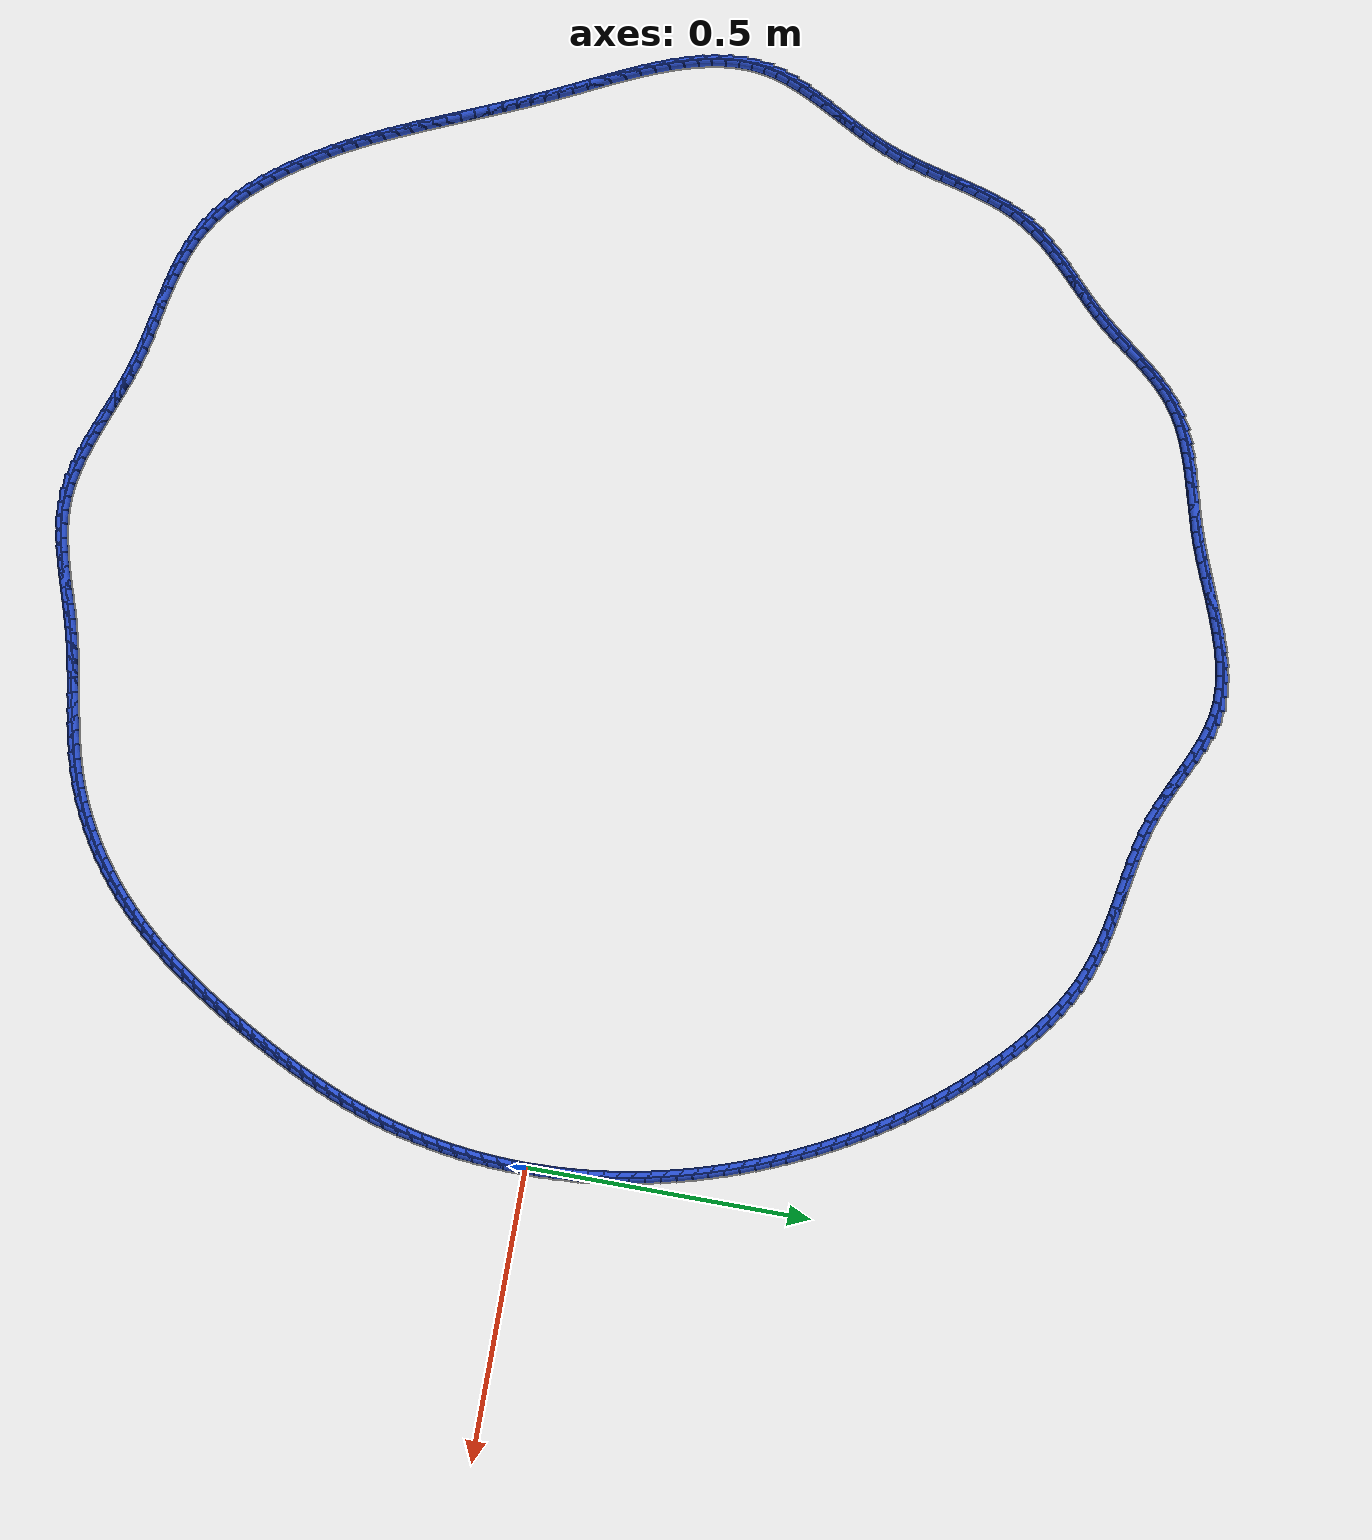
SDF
<sdf version="1.6">
 <world name="default">
  <light name="sun" type="directional">
   <pose>0 0 10 0 -0 0</pose>
   <diffuse>0.8 0.8 0.8 1</diffuse>
   <specular>0.2 0.2 0.2 1</specular>
   <attenuation>
    <range>1000</range>
    <constant>0.9</constant>
    <linear>0.01</linear>
    <quadratic>0.001</quadratic>
   </attenuation>
   <direction>-0.5 0.1 -0.9</direction>
  </light>
  <model name="ground_plane">
   <static>1</static>
   <link name="link">
    <collision name="collision">
     <geometry><plane><normal>0 0 1</normal><size>100 100</size></plane></geometry>
     <surface><friction><ode><mu>100</mu><mu2>50</mu2></ode></friction></surface>
    </collision>
    <visual name="visual">
     <cast_shadows>0</cast_shadows>
     <geometry><plane><normal>0 0 1</normal><size>100 100</size></plane></geometry>
     <material>
      <script><uri>file://media/materials/scripts/gazebo.material</uri><name>Gazebo/WhiteGlow</name></script>
     </material>
    </visual>
   </link>
  </model>
  <gravity>0 0 -9.8</gravity>
  <magnetic_field>6e-06 2.3e-05 -4.2e-05</magnetic_field>
  <atmosphere type="adiabatic"/>
  <physics name="default_physics" default="0" type="ode">
   <max_step_size>0.001</max_step_size>
   <real_time_factor>1</real_time_factor>
   <real_time_update_rate>1000</real_time_update_rate>
  </physics>
  <scene><ambient>0.4 0.4 0.4 1</ambient><background>0.7 0.7 0.7 1</background><shadows>1</shadows></scene>
  <spherical_coordinates>
   <surface_model>EARTH_WGS84</surface_model>
   <latitude_deg>0</latitude_deg>
   <longitude_deg>0</longitude_deg>
   <elevation>0</elevation>
   <heading_deg>0</heading_deg>
  </spherical_coordinates>
  <model name="line">
   <link name="link_0">
    <pose>-1.1275702593849246e-17 -2.0816681711721685e-16 0.01 0 1.57 -1.552094868001441</pose>
    <collision name="collision">
     <geometry><cylinder><radius>0.01</radius><length>0.08</length></cylinder></geometry>
    </collision>
    <visual name="visual">
     <material>
      <script><name>Gazebo/Blue</name><uri>file://media/materials/scripts/gazebo.material</uri></script>
     </material>
     <geometry><cylinder><radius>0.01</radius><length>0.08</length></cylinder></geometry>
    </visual>
   </link>
   <link name="link_1">
    <pose>-0.0005097883931244422 0.027256106887827772 0.01 0 1.57 -1.5250872324449645</pose>
    <collision name="collision">
     <geometry><cylinder><radius>0.01</radius><length>0.08</length></cylinder></geometry>
    </collision>
    <visual name="visual">
     <material>
      <script><name>Gazebo/Blue</name><uri>file://media/materials/scripts/gazebo.material</uri></script>
     </material>
     <geometry><cylinder><radius>0.01</radius><length>0.08</length></cylinder></geometry>
    </visual>
   </link>
   <link name="link_2">
    <pose>-0.0017546198344868726 0.054470918017272996 0.01 0 1.57 -1.4984564545756962</pose>
    <collision name="collision">
     <geometry><cylinder><radius>0.01</radius><length>0.08</length></cylinder></geometry>
    </collision>
    <visual name="visual">
     <material>
      <script><name>Gazebo/Blue</name><uri>file://media/materials/scripts/gazebo.material</uri></script>
     </material>
     <geometry><cylinder><radius>0.01</radius><length>0.08</length></cylinder></geometry>
    </visual>
   </link>
   <link name="link_3">
    <pose>-0.003722848094361998 0.08163151033794203 0.01 0 1.57 -1.472200943007934</pose>
    <collision name="collision">
     <geometry><cylinder><radius>0.01</radius><length>0.08</length></cylinder></geometry>
    </collision>
    <visual name="visual">
     <material>
      <script><name>Gazebo/Blue</name><uri>file://media/materials/scripts/gazebo.material</uri></script>
     </material>
     <geometry><cylinder><radius>0.01</radius><length>0.08</length></cylinder></geometry>
    </visual>
   </link>
   <link name="link_4">
    <pose>-0.006402826943024513 0.10872496079944133 0.01 0 1.57 -1.4463170420218971</pose>
    <collision name="collision">
     <geometry><cylinder><radius>0.01</radius><length>0.08</length></cylinder></geometry>
    </collision>
    <visual name="visual">
     <material>
      <script><name>Gazebo/Blue</name><uri>file://media/materials/scripts/gazebo.material</uri></script>
     </material>
     <geometry><cylinder><radius>0.01</radius><length>0.08</length></cylinder></geometry>
    </visual>
   </link>
   <link name="link_5">
    <pose>-0.009782910150749113 0.1357383463513774 0.01 0 1.57 -1.4207991894194423</pose>
    <collision name="collision">
     <geometry><cylinder><radius>0.01</radius><length>0.08</length></cylinder></geometry>
    </collision>
    <visual name="visual">
     <material>
      <script><name>Gazebo/Blue</name><uri>file://media/materials/scripts/gazebo.material</uri></script>
     </material>
     <geometry><cylinder><radius>0.01</radius><length>0.08</length></cylinder></geometry>
    </visual>
   </link>
   <link name="link_6">
    <pose>-0.013851451487810498 0.16265874394335678 0.01 0 1.57 -1.3956400737274328</pose>
    <collision name="collision">
     <geometry><cylinder><radius>0.01</radius><length>0.08</length></cylinder></geometry>
    </collision>
    <visual name="visual">
     <material>
      <script><name>Gazebo/Blue</name><uri>file://media/materials/scripts/gazebo.material</uri></script>
     </material>
     <geometry><cylinder><radius>0.01</radius><length>0.08</length></cylinder></geometry>
    </visual>
   </link>
   <link name="link_7">
    <pose>-0.018596804724483357 0.18947323052498588 0.01 0 1.57 -1.3708307881304298</pose>
    <collision name="collision">
     <geometry><cylinder><radius>0.01</radius><length>0.08</length></cylinder></geometry>
    </collision>
    <visual name="visual">
     <material>
      <script><name>Gazebo/Blue</name><uri>file://media/materials/scripts/gazebo.material</uri></script>
     </material>
     <geometry><cylinder><radius>0.01</radius><length>0.08</length></cylinder></geometry>
    </visual>
   </link>
   <link name="link_8">
    <pose>-0.024007323631042393 0.21616888304587134 0.01 0 1.57 -1.346360978987845</pose>
    <collision name="collision">
     <geometry><cylinder><radius>0.01</radius><length>0.08</length></cylinder></geometry>
    </collision>
    <visual name="visual">
     <material>
      <script><name>Gazebo/Blue</name><uri>file://media/materials/scripts/gazebo.material</uri></script>
     </material>
     <geometry><cylinder><radius>0.01</radius><length>0.08</length></cylinder></geometry>
    </visual>
   </link>
   <link name="link_9">
    <pose>-0.030071361977762293 0.24273277845561952 0.01 0 1.57 -1.3222181247419766</pose>
    <collision name="collision">
     <geometry><cylinder><radius>0.01</radius><length>0.08</length></cylinder></geometry>
    </collision>
    <visual name="visual">
     <material>
      <script><name>Gazebo/Blue</name><uri>file://media/materials/scripts/gazebo.material</uri></script>
     </material>
     <geometry><cylinder><radius>0.01</radius><length>0.08</length></cylinder></geometry>
    </visual>
   </link>
   <link name="link_10">
    <pose>-0.03677728899681782 0.2691519590634196 0.01 0 1.57 -1.2983530634299068</pose>
    <collision name="collision">
     <geometry><cylinder><radius>0.01</radius><length>0.08</length></cylinder></geometry>
    </collision>
    <visual name="visual">
     <material>
      <script><name>Gazebo/Blue</name><uri>file://media/materials/scripts/gazebo.material</uri></script>
     </material>
     <geometry><cylinder><radius>0.01</radius><length>0.08</length></cylinder></geometry>
    </visual>
   </link>
   <link name="link_11">
    <pose>-0.044114105184688876 0.2954120529112052 0.01 0 1.57 -1.2746993457583078</pose>
    <collision name="collision">
     <geometry><cylinder><radius>0.01</radius><length>0.08</length></cylinder></geometry>
    </collision>
    <visual name="visual">
     <material>
      <script><name>Gazebo/Blue</name><uri>file://media/materials/scripts/gazebo.material</uri></script>
     </material>
     <geometry><cylinder><radius>0.01</radius><length>0.08</length></cylinder></geometry>
    </visual>
   </link>
   <link name="link_12">
    <pose>-0.052071648974059206 0.3214968107515941 0.01 0 1.57 -1.2512318086805811</pose>
    <collision name="collision">
     <geometry><cylinder><radius>0.01</radius><length>0.08</length></cylinder></geometry>
    </collision>
    <visual name="visual">
     <material>
      <script><name>Gazebo/Blue</name><uri>file://media/materials/scripts/gazebo.material</uri></script>
     </material>
     <geometry><cylinder><radius>0.01</radius><length>0.08</length></cylinder></geometry>
    </visual>
   </link>
   <link name="link_13">
    <pose>-0.06063981663602372 0.34738985375761167 0.01 0 1.57 -1.2279280655758262</pose>
    <collision name="collision">
     <geometry><cylinder><radius>0.01</radius><length>0.08</length></cylinder></geometry>
    </collision>
    <visual name="visual">
     <material>
      <script><name>Gazebo/Blue</name><uri>file://media/materials/scripts/gazebo.material</uri></script>
     </material>
     <geometry><cylinder><radius>0.01</radius><length>0.08</length></cylinder></geometry>
    </visual>
   </link>
   <link name="link_14">
    <pose>-0.06980850444167744 0.37307480310228397 0.01 0 1.57 -1.2047653316231555</pose>
    <collision name="collision">
     <geometry><cylinder><radius>0.01</radius><length>0.08</length></cylinder></geometry>
    </collision>
    <visual name="visual">
     <material>
      <script><name>Gazebo/Blue</name><uri>file://media/materials/scripts/gazebo.material</uri></script>
     </material>
     <geometry><cylinder><radius>0.01</radius><length>0.08</length></cylinder></geometry>
    </visual>
   </link>
   <link name="link_15">
    <pose>-0.07956760866211533 0.39853527995863636 0.01 0 1.57 -1.1817204668004173</pose>
    <collision name="collision">
     <geometry><cylinder><radius>0.01</radius><length>0.08</length></cylinder></geometry>
    </collision>
    <visual name="visual">
     <material>
      <script><name>Gazebo/Blue</name><uri>file://media/materials/scripts/gazebo.material</uri></script>
     </material>
     <geometry><cylinder><radius>0.01</radius><length>0.08</length></cylinder></geometry>
    </visual>
   </link>
   <link name="link_16">
    <pose>-0.08990702556843236 0.42375490549969463 0.01 0 1.57 -1.1587700111801744</pose>
    <collision name="collision">
     <geometry><cylinder><radius>0.01</radius><length>0.08</length></cylinder></geometry>
    </collision>
    <visual name="visual">
     <material>
      <script><name>Gazebo/Blue</name><uri>file://media/materials/scripts/gazebo.material</uri></script>
     </material>
     <geometry><cylinder><radius>0.01</radius><length>0.08</length></cylinder></geometry>
    </visual>
   </link>
   <link name="link_17">
    <pose>-0.10081665143172355 0.44871730089848466 0.01 0 1.57 -1.135890213580655</pose>
    <collision name="collision">
     <geometry><cylinder><radius>0.01</radius><length>0.08</length></cylinder></geometry>
    </collision>
    <visual name="visual">
     <material>
      <script><name>Gazebo/Blue</name><uri>file://media/materials/scripts/gazebo.material</uri></script>
     </material>
     <geometry><cylinder><radius>0.01</radius><length>0.08</length></cylinder></geometry>
    </visual>
   </link>
   <link name="link_18">
    <pose>-0.11228638252308387 0.4734060873280317 0.01 0 1.57 -1.113057054642454</pose>
    <collision name="collision">
     <geometry><cylinder><radius>0.01</radius><length>0.08</length></cylinder></geometry>
    </collision>
    <visual name="visual">
     <material>
      <script><name>Gazebo/Blue</name><uri>file://media/materials/scripts/gazebo.material</uri></script>
     </material>
     <geometry><cylinder><radius>0.01</radius><length>0.08</length></cylinder></geometry>
    </visual>
   </link>
   <link name="link_19">
    <pose>-0.12430611511360823 0.4978048859613617 0.01 0 1.57 -1.0902462654132137</pose>
    <collision name="collision">
     <geometry><cylinder><radius>0.01</radius><length>0.08</length></cylinder></geometry>
    </collision>
    <visual name="visual">
     <material>
      <script><name>Gazebo/Blue</name><uri>file://media/materials/scripts/gazebo.material</uri></script>
     </material>
     <geometry><cylinder><radius>0.01</radius><length>0.08</length></cylinder></geometry>
    </visual>
   </link>
   <link name="link_20">
    <pose>-0.13686574547439168 0.5218973179715002 0.01 0 1.57 -1.0674228626646705</pose>
    <collision name="collision">
     <geometry><cylinder><radius>0.01</radius><length>0.08</length></cylinder></geometry>
    </collision>
    <visual name="visual">
     <material>
      <script><name>Gazebo/Blue</name><uri>file://media/materials/scripts/gazebo.material</uri></script>
     </material>
     <geometry><cylinder><radius>0.01</radius><length>0.08</length></cylinder></geometry>
    </visual>
   </link>
   <link name="link_21">
    <pose>-0.14995568107336096 0.5456673432919278 0.01 0 1.57 -1.044369132323076</pose>
    <collision name="collision">
     <geometry><cylinder><radius>0.01</radius><length>0.08</length></cylinder></geometry>
    </collision>
    <visual name="visual">
     <material>
      <script><name>Gazebo/Blue</name><uri>file://media/materials/scripts/gazebo.material</uri></script>
     </material>
     <geometry><cylinder><radius>0.01</radius><length>0.08</length></cylinder></geometry>
    </visual>
   </link>
   <link name="link_22">
    <pose>-0.16357623414456696 0.5691054855569764 0.01 0 1.57 -1.020920529568022</pose>
    <collision name="collision">
     <geometry><cylinder><radius>0.01</radius><length>0.08</length></cylinder></geometry>
    </collision>
    <visual name="visual">
     <material>
      <script><name>Gazebo/Blue</name><uri>file://media/materials/scripts/gazebo.material</uri></script>
     </material>
     <geometry><cylinder><radius>0.01</radius><length>0.08</length></cylinder></geometry>
    </visual>
   </link>
   <link name="link_23">
    <pose>-0.1777366901418348 0.5922082147837116 0.01 0 1.57 -0.9971010919846204</pose>
    <collision name="collision">
     <geometry><cylinder><radius>0.01</radius><length>0.08</length></cylinder></geometry>
    </collision>
    <visual name="visual">
     <material>
      <script><name>Gazebo/Blue</name><uri>file://media/materials/scripts/gazebo.material</uri></script>
     </material>
     <geometry><cylinder><radius>0.01</radius><length>0.08</length></cylinder></geometry>
    </visual>
   </link>
   <link name="link_24">
    <pose>-0.19244665883658618 0.6149722159083256 0.01 0 1.57 -0.9729441683533719</pose>
    <collision name="collision">
     <geometry><cylinder><radius>0.01</radius><length>0.08</length></cylinder></geometry>
    </collision>
    <visual name="visual">
     <material>
      <script><name>Gazebo/Blue</name><uri>file://media/materials/scripts/gazebo.material</uri></script>
     </material>
     <geometry><cylinder><radius>0.01</radius><length>0.08</length></cylinder></geometry>
    </visual>
   </link>
   <link name="link_25">
    <pose>-0.20771575000024242 0.6373941738670104 0.01 0 1.57 -0.9484855985346091</pose>
    <collision name="collision">
     <geometry><cylinder><radius>0.01</radius><length>0.08</length></cylinder></geometry>
    </collision>
    <visual name="visual">
     <material>
      <script><name>Gazebo/Blue</name><uri>file://media/materials/scripts/gazebo.material</uri></script>
     </material>
     <geometry><cylinder><radius>0.01</radius><length>0.08</length></cylinder></geometry>
    </visual>
   </link>
   <link name="link_26">
    <pose>-0.22355357340422538 0.6594707735959585 0.01 0 1.57 -0.9237634932367614</pose>
    <collision name="collision">
     <geometry><cylinder><radius>0.01</radius><length>0.08</length></cylinder></geometry>
    </collision>
    <visual name="visual">
     <material>
      <script><name>Gazebo/Blue</name><uri>file://media/materials/scripts/gazebo.material</uri></script>
     </material>
     <geometry><cylinder><radius>0.01</radius><length>0.08</length></cylinder></geometry>
    </visual>
   </link>
   <link name="link_27">
    <pose>-0.23996973881995637 0.6811987000313618 0.01 0 1.57 -0.8988179671849132</pose>
    <collision name="collision">
     <geometry><cylinder><radius>0.01</radius><length>0.08</length></cylinder></geometry>
    </collision>
    <visual name="visual">
     <material>
      <script><name>Gazebo/Blue</name><uri>file://media/materials/scripts/gazebo.material</uri></script>
     </material>
     <geometry><cylinder><radius>0.01</radius><length>0.08</length></cylinder></geometry>
    </visual>
   </link>
   <link name="link_28">
    <pose>-0.2569738560188572 0.702574638109413 0.01 0 1.57 -0.8736908293880754</pose>
    <collision name="collision">
     <geometry><cylinder><radius>0.01</radius><length>0.08</length></cylinder></geometry>
    </collision>
    <visual name="visual">
     <material>
      <script><name>Gazebo/Blue</name><uri>file://media/materials/scripts/gazebo.material</uri></script>
     </material>
     <geometry><cylinder><radius>0.01</radius><length>0.08</length></cylinder></geometry>
    </visual>
   </link>
   <link name="link_29">
    <pose>-0.2745755347723494 0.7235952727663041 0.01 0 1.57 -0.8484252358404707</pose>
    <collision name="collision">
     <geometry><cylinder><radius>0.01</radius><length>0.08</length></cylinder></geometry>
    </collision>
    <visual name="visual">
     <material>
      <script><name>Gazebo/Blue</name><uri>file://media/materials/scripts/gazebo.material</uri></script>
     </material>
     <geometry><cylinder><radius>0.01</radius><length>0.08</length></cylinder></geometry>
    </visual>
   </link>
   <link name="link_30">
    <pose>-0.29278438485185454 0.7442572889382272 0.01 0 1.57 -0.8226770624096985</pose>
    <collision name="collision">
     <geometry><cylinder><radius>0.01</radius><length>0.08</length></cylinder></geometry>
    </collision>
    <visual name="visual">
     <material>
      <script><name>Gazebo/Blue</name><uri>file://media/materials/scripts/gazebo.material</uri></script>
     </material>
     <geometry><cylinder><radius>0.01</radius><length>0.08</length></cylinder></geometry>
    </visual>
   </link>
   <link name="link_31">
    <pose>-0.3116089252288883 0.7645403950459768 0.01 0 1.57 -0.794368511000852</pose>
    <collision name="collision">
     <geometry><cylinder><radius>0.01</radius><length>0.08</length></cylinder></geometry>
    </collision>
    <visual name="visual">
     <material>
      <script><name>Gazebo/Blue</name><uri>file://media/materials/scripts/gazebo.material</uri></script>
     </material>
     <geometry><cylinder><radius>0.01</radius><length>0.08</length></cylinder></geometry>
    </visual>
   </link>
   <link name="link_32">
    <pose>-0.3310519642243161 0.7843354225786678 0.01 0 1.57 -0.7626220650256759</pose>
    <collision name="collision">
     <geometry><cylinder><radius>0.01</radius><length>0.08</length></cylinder></geometry>
    </collision>
    <visual name="visual">
     <material>
      <script><name>Gazebo/Blue</name><uri>file://media/materials/scripts/gazebo.material</uri></script>
     </material>
     <geometry><cylinder><radius>0.01</radius><length>0.08</length></cylinder></geometry>
    </visual>
   </link>
   <link name="link_33">
    <pose>-0.3511144476446857 0.8035042160381425 0.01 0 1.57 -0.7271717948714365</pose>
    <collision name="collision">
     <geometry><cylinder><radius>0.01</radius><length>0.08</length></cylinder></geometry>
    </collision>
    <visual name="visual">
     <material>
      <script><name>Gazebo/Blue</name><uri>file://media/materials/scripts/gazebo.material</uri></script>
     </material>
     <geometry><cylinder><radius>0.01</radius><length>0.08</length></cylinder></geometry>
    </visual>
   </link>
   <link name="link_34">
    <pose>-0.37179732026817386 0.8219086039213293 0.01 0 1.57 -0.6877252574277032</pose>
    <collision name="collision">
     <geometry><cylinder><radius>0.01</radius><length>0.08</length></cylinder></geometry>
    </collision>
    <visual name="visual">
     <material>
      <script><name>Gazebo/Blue</name><uri>file://media/materials/scripts/gazebo.material</uri></script>
     </material>
     <geometry><cylinder><radius>0.01</radius><length>0.08</length></cylinder></geometry>
    </visual>
   </link>
   <link name="link_35">
    <pose>-0.3931015268729575 0.839410414725156 0.01 0 1.57 -0.6439737413709179</pose>
    <collision name="collision">
     <geometry><cylinder><radius>0.01</radius><length>0.08</length></cylinder></geometry>
    </collision>
    <visual name="visual">
     <material>
      <script><name>Gazebo/Blue</name><uri>file://media/materials/scripts/gazebo.material</uri></script>
     </material>
     <geometry><cylinder><radius>0.01</radius><length>0.08</length></cylinder></geometry>
    </visual>
   </link>
   <link name="link_36">
    <pose>-0.41502801223721314 0.8558714769465512 0.01 0 1.57 -0.5956084304087684</pose>
    <collision name="collision">
     <geometry><cylinder><radius>0.01</radius><length>0.08</length></cylinder></geometry>
    </collision>
    <visual name="visual">
     <material>
      <script><name>Gazebo/Blue</name><uri>file://media/materials/scripts/gazebo.material</uri></script>
     </material>
     <geometry><cylinder><radius>0.01</radius><length>0.08</length></cylinder></geometry>
    </visual>
   </link>
   <link name="link_37">
    <pose>-0.4375777211391178 0.871153619082443 0.01 0 1.57 -0.5423440183714935</pose>
    <collision name="collision">
     <geometry><cylinder><radius>0.01</radius><length>0.08</length></cylinder></geometry>
    </collision>
    <visual name="visual">
     <material>
      <script><name>Gazebo/Blue</name><uri>file://media/materials/scripts/gazebo.material</uri></script>
     </material>
     <geometry><cylinder><radius>0.01</radius><length>0.08</length></cylinder></geometry>
    </visual>
   </link>
   <link name="link_38">
    <pose>-0.46075159835684815 0.8851186696297596 0.01 0 1.57 -0.4839514217598005</pose>
    <collision name="collision">
     <geometry><cylinder><radius>0.01</radius><length>0.08</length></cylinder></geometry>
    </collision>
    <visual name="visual">
     <material>
      <script><name>Gazebo/Blue</name><uri>file://media/materials/scripts/gazebo.material</uri></script>
     </material>
     <geometry><cylinder><radius>0.01</radius><length>0.08</length></cylinder></geometry>
    </visual>
   </link>
   <link name="link_39">
    <pose>-0.4845505886685809 0.897628457085429 0.01 0 1.57 -0.42030517239447834</pose>
    <collision name="collision">
     <geometry><cylinder><radius>0.01</radius><length>0.08</length></cylinder></geometry>
    </collision>
    <visual name="visual">
     <material>
      <script><name>Gazebo/Blue</name><uri>file://media/materials/scripts/gazebo.material</uri></script>
     </material>
     <geometry><cylinder><radius>0.01</radius><length>0.08</length></cylinder></geometry>
    </visual>
   </link>
   <link name="link_40">
    <pose>-0.5089756089896693 0.9085449421616819 0.01 0 1.57 -0.35529582634054047</pose>
    <collision name="collision">
     <geometry><cylinder><radius>0.01</radius><length>0.08</length></cylinder></geometry>
    </collision>
    <visual name="visual">
     <material>
      <script><name>Gazebo/Blue</name><uri>file://media/materials/scripts/gazebo.material</uri></script>
     </material>
     <geometry><cylinder><radius>0.01</radius><length>0.08</length></cylinder></geometry>
    </visual>
   </link>
   <link name="link_41">
    <pose>-0.5340060410290537 0.9178322749208846 0.01 0 1.57 -0.30006851788065747</pose>
    <collision name="collision">
     <geometry><cylinder><radius>0.01</radius><length>0.08</length></cylinder></geometry>
    </collision>
    <visual name="visual">
     <material>
      <script><name>Gazebo/Blue</name><uri>file://media/materials/scripts/gazebo.material</uri></script>
     </material>
     <geometry><cylinder><radius>0.01</radius><length>0.08</length></cylinder></geometry>
    </visual>
   </link>
   <link name="link_42">
    <pose>-0.5595612601018097 0.9257393491272026 0.01 0 1.57 -0.25680905375745994</pose>
    <collision name="collision">
     <geometry><cylinder><radius>0.01</radius><length>0.08</length></cylinder></geometry>
    </collision>
    <visual name="visual">
     <material>
      <script><name>Gazebo/Blue</name><uri>file://media/materials/scripts/gazebo.material</uri></script>
     </material>
     <geometry><cylinder><radius>0.01</radius><length>0.08</length></cylinder></geometry>
    </visual>
   </link>
   <link name="link_43">
    <pose>-0.5855502722677202 0.9325642629703106 0.01 0 1.57 -0.22551051430375543</pose>
    <collision name="collision">
     <geometry><cylinder><radius>0.01</radius><length>0.08</length></cylinder></geometry>
    </collision>
    <visual name="visual">
     <material>
      <script><name>Gazebo/Blue</name><uri>file://media/materials/scripts/gazebo.material</uri></script>
     </material>
     <geometry><cylinder><radius>0.01</radius><length>0.08</length></cylinder></geometry>
    </visual>
   </link>
   <link name="link_44">
    <pose>-0.6118820835865675 0.938605114639884 0.01 0 1.57 -0.20599501821255786</pose>
    <collision name="collision">
     <geometry><cylinder><radius>0.01</radius><length>0.08</length></cylinder></geometry>
    </collision>
    <visual name="visual">
     <material>
      <script><name>Gazebo/Blue</name><uri>file://media/materials/scripts/gazebo.material</uri></script>
     </material>
     <geometry><cylinder><radius>0.01</radius><length>0.08</length></cylinder></geometry>
    </visual>
   </link>
   <link name="link_45">
    <pose>-0.6384657001181342 0.9441600023255977 0.01 0 1.57 -0.19804752755272131</pose>
    <collision name="collision">
     <geometry><cylinder><radius>0.01</radius><length>0.08</length></cylinder></geometry>
    </collision>
    <visual name="visual">
     <material>
      <script><name>Gazebo/Blue</name><uri>file://media/materials/scripts/gazebo.material</uri></script>
     </material>
     <geometry><cylinder><radius>0.01</radius><length>0.08</length></cylinder></geometry>
    </visual>
   </link>
   <link name="link_46">
    <pose>-0.6652101279222029 0.9495270242171271 0.01 0 1.57 -0.20149465928132004</pose>
    <collision name="collision">
     <geometry><cylinder><radius>0.01</radius><length>0.08</length></cylinder></geometry>
    </collision>
    <visual name="visual">
     <material>
      <script><name>Gazebo/Blue</name><uri>file://media/materials/scripts/gazebo.material</uri></script>
     </material>
     <geometry><cylinder><radius>0.01</radius><length>0.08</length></cylinder></geometry>
    </visual>
   </link>
   <link name="link_47">
    <pose>-0.6920243730585564 0.9550042785041474 0.01 0 1.57 -0.2162337912938419</pose>
    <collision name="collision">
     <geometry><cylinder><radius>0.01</radius><length>0.08</length></cylinder></geometry>
    </collision>
    <visual name="visual">
     <material>
      <script><name>Gazebo/Blue</name><uri>file://media/materials/scripts/gazebo.material</uri></script>
     </material>
     <geometry><cylinder><radius>0.01</radius><length>0.08</length></cylinder></geometry>
    </visual>
   </link>
   <link name="link_48">
    <pose>-0.7188174415869772 0.9608898633763336 0.01 0 1.57 -0.24221785541856167</pose>
    <collision name="collision">
     <geometry><cylinder><radius>0.01</radius><length>0.08</length></cylinder></geometry>
    </collision>
    <visual name="visual">
     <material>
      <script><name>Gazebo/Blue</name><uri>file://media/materials/scripts/gazebo.material</uri></script>
     </material>
     <geometry><cylinder><radius>0.01</radius><length>0.08</length></cylinder></geometry>
    </visual>
   </link>
   <link name="link_49">
    <pose>-0.7454983395672478 0.9674818770233611 0.01 0 1.57 -0.2793982940271897</pose>
    <collision name="collision">
     <geometry><cylinder><radius>0.01</radius><length>0.08</length></cylinder></geometry>
    </collision>
    <visual name="visual">
     <material>
      <script><name>Gazebo/Blue</name><uri>file://media/materials/scripts/gazebo.material</uri></script>
     </material>
     <geometry><cylinder><radius>0.01</radius><length>0.08</length></cylinder></geometry>
    </visual>
   </link>
   <link name="link_50">
    <pose>-0.7719760730591512 0.9750784176349052 0.01 0 1.57 -0.32762724917651614</pose>
    <collision name="collision">
     <geometry><cylinder><radius>0.01</radius><length>0.08</length></cylinder></geometry>
    </collision>
    <visual name="visual">
     <material>
      <script><name>Gazebo/Blue</name><uri>file://media/materials/scripts/gazebo.material</uri></script>
     </material>
     <geometry><cylinder><radius>0.01</radius><length>0.08</length></cylinder></geometry>
    </visual>
   </link>
   <link name="link_51">
    <pose>-0.7981596481224692 0.9839775834006405 0.01 0 1.57 -0.38388838480037374</pose>
    <collision name="collision">
     <geometry><cylinder><radius>0.01</radius><length>0.08</length></cylinder></geometry>
    </collision>
    <visual name="visual">
     <material>
      <script><name>Gazebo/Blue</name><uri>file://media/materials/scripts/gazebo.material</uri></script>
     </material>
     <geometry><cylinder><radius>0.01</radius><length>0.08</length></cylinder></geometry>
    </visual>
   </link>
   <link name="link_52">
    <pose>-0.8239720446473375 0.9944039449346422 0.01 0 1.57 -0.42797222812863983</pose>
    <collision name="collision">
     <geometry><cylinder><radius>0.01</radius><length>0.08</length></cylinder></geometry>
    </collision>
    <visual name="visual">
     <material>
      <script><name>Gazebo/Blue</name><uri>file://media/materials/scripts/gazebo.material</uri></script>
     </material>
     <geometry><cylinder><radius>0.01</radius><length>0.08</length></cylinder></geometry>
    </visual>
   </link>
   <link name="link_53">
    <pose>-0.8494425330680174 1.006022792695016 0.01 0 1.57 -0.4513946037116816</pose>
    <collision name="collision">
     <geometry><cylinder><radius>0.01</radius><length>0.08</length></cylinder></geometry>
    </collision>
    <visual name="visual">
     <material>
      <script><name>Gazebo/Blue</name><uri>file://media/materials/scripts/gazebo.material</uri></script>
     </material>
     <geometry><cylinder><radius>0.01</radius><length>0.08</length></cylinder></geometry>
    </visual>
   </link>
   <link name="link_54">
    <pose>-0.8746492295364838 1.0182424004800605 0.01 0 1.57 -0.4545470770778671</pose>
    <collision name="collision">
     <geometry><cylinder><radius>0.01</radius><length>0.08</length></cylinder></geometry>
    </collision>
    <visual name="visual">
     <material>
      <script><name>Gazebo/Blue</name><uri>file://media/materials/scripts/gazebo.material</uri></script>
     </material>
     <geometry><cylinder><radius>0.01</radius><length>0.08</length></cylinder></geometry>
    </visual>
   </link>
   <link name="link_55">
    <pose>-0.8996705076663845 1.0304696873748564 0.01 0 1.57 -0.4371294426050382</pose>
    <collision name="collision">
     <geometry><cylinder><radius>0.01</radius><length>0.08</length></cylinder></geometry>
    </collision>
    <visual name="visual">
     <material>
      <script><name>Gazebo/Blue</name><uri>file://media/materials/scripts/gazebo.material</uri></script>
     </material>
     <geometry><cylinder><radius>0.01</radius><length>0.08</length></cylinder></geometry>
    </visual>
   </link>
   <link name="link_56">
    <pose>-0.9245847410713676 1.0421115724644856 0.01 0 1.57 -0.39801959434615647</pose>
    <collision name="collision">
     <geometry><cylinder><radius>0.01</radius><length>0.08</length></cylinder></geometry>
    </collision>
    <visual name="visual">
     <material>
      <script><name>Gazebo/Blue</name><uri>file://media/materials/scripts/gazebo.material</uri></script>
     </material>
     <geometry><cylinder><radius>0.01</radius><length>0.08</length></cylinder></geometry>
    </visual>
   </link>
   <link name="link_57">
    <pose>-0.9494703033650808 1.052574974834028 0.01 0 1.57 -0.3354057981611847</pose>
    <collision name="collision">
     <geometry><cylinder><radius>0.01</radius><length>0.08</length></cylinder></geometry>
    </collision>
    <visual name="visual">
     <material>
      <script><name>Gazebo/Blue</name><uri>file://media/materials/scripts/gazebo.material</uri></script>
     </material>
     <geometry><cylinder><radius>0.01</radius><length>0.08</length></cylinder></geometry>
    </visual>
   </link>
   <link name="link_58">
    <pose>-0.9744055681611726 1.0612668135685657 0.01 0 1.57 -0.24728147892631172</pose>
    <collision name="collision">
     <geometry><cylinder><radius>0.01</radius><length>0.08</length></cylinder></geometry>
    </collision>
    <visual name="visual">
     <material>
      <script><name>Gazebo/Blue</name><uri>file://media/materials/scripts/gazebo.material</uri></script>
     </material>
     <geometry><cylinder><radius>0.01</radius><length>0.08</length></cylinder></geometry>
    </visual>
   </link>
   <link name="link_59">
    <pose>-0.9994689090732907 1.0675940077531796 0.01 0 1.57 -0.1352908183445229</pose>
    <collision name="collision">
     <geometry><cylinder><radius>0.01</radius><length>0.08</length></cylinder></geometry>
    </collision>
    <visual name="visual">
     <material>
      <script><name>Gazebo/Blue</name><uri>file://media/materials/scripts/gazebo.material</uri></script>
     </material>
     <geometry><cylinder><radius>0.01</radius><length>0.08</length></cylinder></geometry>
    </visual>
   </link>
   <link name="link_60">
    <pose>-1.0247325221904307 1.0710329499741589 0.01 0 1.57 -0.023708304292810196</pose>
    <collision name="collision">
     <geometry><cylinder><radius>0.01</radius><length>0.08</length></cylinder></geometry>
    </collision>
    <visual name="visual">
     <material>
      <script><name>Gazebo/Blue</name><uri>file://media/materials/scripts/gazebo.material</uri></script>
     </material>
     <geometry><cylinder><radius>0.01</radius><length>0.08</length></cylinder></geometry>
    </visual>
   </link>
   <link name="link_61">
    <pose>-1.0502172767384688 1.071637263518984 0.01 0 1.57 0.07343296345596102</pose>
    <collision name="collision">
     <geometry><cylinder><radius>0.01</radius><length>0.08</length></cylinder></geometry>
    </collision>
    <visual name="visual">
     <material>
      <script><name>Gazebo/Blue</name><uri>file://media/materials/scripts/gazebo.material</uri></script>
     </material>
     <geometry><cylinder><radius>0.01</radius><length>0.08</length></cylinder></geometry>
    </visual>
   </link>
   <link name="link_62">
    <pose>-1.0759186140235304 1.0697465384195703 0.01 0 1.57 0.1548156123089967</pose>
    <collision name="collision">
     <geometry><cylinder><radius>0.01</radius><length>0.08</length></cylinder></geometry>
    </collision>
    <visual name="visual">
     <material>
      <script><name>Gazebo/Blue</name><uri>file://media/materials/scripts/gazebo.material</uri></script>
     </material>
     <geometry><cylinder><radius>0.01</radius><length>0.08</length></cylinder></geometry>
    </visual>
   </link>
   <link name="link_63">
    <pose>-1.1018317932852302 1.06570241225901 0.01 0 1.57 0.22054275431965478</pose>
    <collision name="collision">
     <geometry><cylinder><radius>0.01</radius><length>0.08</length></cylinder></geometry>
    </collision>
    <visual name="visual">
     <material>
      <script><name>Gazebo/Blue</name><uri>file://media/materials/scripts/gazebo.material</uri></script>
     </material>
     <geometry><cylinder><radius>0.01</radius><length>0.08</length></cylinder></geometry>
    </visual>
   </link>
   <link name="link_64">
    <pose>-1.1279520737631834 1.0598465226203937 0.01 0 1.57 0.27144656843689907</pose>
    <collision name="collision">
     <geometry><cylinder><radius>0.01</radius><length>0.08</length></cylinder></geometry>
    </collision>
    <visual name="visual">
     <material>
      <script><name>Gazebo/Blue</name><uri>file://media/materials/scripts/gazebo.material</uri></script>
     </material>
     <geometry><cylinder><radius>0.01</radius><length>0.08</length></cylinder></geometry>
    </visual>
   </link>
   <link name="link_65">
    <pose>-1.1542747146970058 1.0525205070868136 0.01 0 1.57 0.308608717847206</pose>
    <collision name="collision">
     <geometry><cylinder><radius>0.01</radius><length>0.08</length></cylinder></geometry>
    </collision>
    <visual name="visual">
     <material>
      <script><name>Gazebo/Blue</name><uri>file://media/materials/scripts/gazebo.material</uri></script>
     </material>
     <geometry><cylinder><radius>0.01</radius><length>0.08</length></cylinder></geometry>
    </visual>
   </link>
   <link name="link_66">
    <pose>-1.1807949753263123 1.0440660032413613 0.01 0 1.57 0.3330603810830687</pose>
    <collision name="collision">
     <geometry><cylinder><radius>0.01</radius><length>0.08</length></cylinder></geometry>
    </collision>
    <visual name="visual">
     <material>
      <script><name>Gazebo/Blue</name><uri>file://media/materials/scripts/gazebo.material</uri></script>
     </material>
     <geometry><cylinder><radius>0.01</radius><length>0.08</length></cylinder></geometry>
    </visual>
   </link>
   <link name="link_67">
    <pose>-1.2075081148907183 1.0348246486671286 0.01 0 1.57 0.3456249403016464</pose>
    <collision name="collision">
     <geometry><cylinder><radius>0.01</radius><length>0.08</length></cylinder></geometry>
    </collision>
    <visual name="visual">
     <material>
      <script><name>Gazebo/Blue</name><uri>file://media/materials/scripts/gazebo.material</uri></script>
     </material>
     <geometry><cylinder><radius>0.01</radius><length>0.08</length></cylinder></geometry>
    </visual>
   </link>
   <link name="link_68">
    <pose>-1.234409392629839 1.0251380809472073 0.01 0 1.57 0.34685127926090076</pose>
    <collision name="collision">
     <geometry><cylinder><radius>0.01</radius><length>0.08</length></cylinder></geometry>
    </collision>
    <visual name="visual">
     <material>
      <script><name>Gazebo/Blue</name><uri>file://media/materials/scripts/gazebo.material</uri></script>
     </material>
     <geometry><cylinder><radius>0.01</radius><length>0.08</length></cylinder></geometry>
    </visual>
   </link>
   <link name="link_69">
    <pose>-1.2614940677832898 1.0153479376646888 0.01 0 1.57 0.33699877376147974</pose>
    <collision name="collision">
     <geometry><cylinder><radius>0.01</radius><length>0.08</length></cylinder></geometry>
    </collision>
    <visual name="visual">
     <material>
      <script><name>Gazebo/Blue</name><uri>file://media/materials/scripts/gazebo.material</uri></script>
     </material>
     <geometry><cylinder><radius>0.01</radius><length>0.08</length></cylinder></geometry>
    </visual>
   </link>
   <link name="link_70">
    <pose>-1.2887573995906862 1.0057958564026643 0.01 0 1.57 0.31605299089268024</pose>
    <collision name="collision">
     <geometry><cylinder><radius>0.01</radius><length>0.08</length></cylinder></geometry>
    </collision>
    <visual name="visual">
     <material>
      <script><name>Gazebo/Blue</name><uri>file://media/materials/scripts/gazebo.material</uri></script>
     </material>
     <geometry><cylinder><radius>0.01</radius><length>0.08</length></cylinder></geometry>
    </visual>
   </link>
   <link name="link_71">
    <pose>-1.3161946472916428 0.996823474744226 0.01 0 1.57 0.28464280241152184</pose>
    <collision name="collision">
     <geometry><cylinder><radius>0.01</radius><length>0.08</length></cylinder></geometry>
    </collision>
    <visual name="visual">
     <material>
      <script><name>Gazebo/Blue</name><uri>file://media/materials/scripts/gazebo.material</uri></script>
     </material>
     <geometry><cylinder><radius>0.01</radius><length>0.08</length></cylinder></geometry>
    </visual>
   </link>
   <link name="link_72">
    <pose>-1.3437951036640556 0.9887479183227346 0.01 0 1.57 0.2561344135629516</pose>
    <collision name="collision">
     <geometry><cylinder><radius>0.01</radius><length>0.08</length></cylinder></geometry>
    </collision>
    <visual name="visual">
     <material>
      <script><name>Gazebo/Blue</name><uri>file://media/materials/scripts/gazebo.material</uri></script>
     </material>
     <geometry><cylinder><radius>0.01</radius><length>0.08</length></cylinder></geometry>
    </visual>
   </link>
   <link name="link_73">
    <pose>-1.3714550393645775 0.9815041510035148 0.01 0 1.57 0.24134460972041816</pose>
    <collision name="collision">
     <geometry><cylinder><radius>0.01</radius><length>0.08</length></cylinder></geometry>
    </collision>
    <visual name="visual">
     <material>
      <script><name>Gazebo/Blue</name><uri>file://media/materials/scripts/gazebo.material</uri></script>
     </material>
     <geometry><cylinder><radius>0.01</radius><length>0.08</length></cylinder></geometry>
    </visual>
   </link>
   <link name="link_74">
    <pose>-1.3989971507585357 0.9747248721917928 0.01 0 1.57 0.2407979713594593</pose>
    <collision name="collision">
     <geometry><cylinder><radius>0.01</radius><length>0.08</length></cylinder></geometry>
    </collision>
    <visual name="visual">
     <material>
      <script><name>Gazebo/Blue</name><uri>file://media/materials/scripts/gazebo.material</uri></script>
     </material>
     <geometry><cylinder><radius>0.01</radius><length>0.08</length></cylinder></geometry>
    </visual>
   </link>
   <link name="link_75">
    <pose>-1.4262421245115504 0.9680345248653577 0.01 0 1.57 0.2549683180707337</pose>
    <collision name="collision">
     <geometry><cylinder><radius>0.01</radius><length>0.08</length></cylinder></geometry>
    </collision>
    <visual name="visual">
     <material>
      <script><name>Gazebo/Blue</name><uri>file://media/materials/scripts/gazebo.material</uri></script>
     </material>
     <geometry><cylinder><radius>0.01</radius><length>0.08</length></cylinder></geometry>
    </visual>
   </link>
   <link name="link_76">
    <pose>-1.4530106472892392 0.9610575520019974 0.01 0 1.57 0.28460333692492545</pose>
    <collision name="collision">
     <geometry><cylinder><radius>0.01</radius><length>0.08</length></cylinder></geometry>
    </collision>
    <visual name="visual">
     <material>
      <script><name>Gazebo/Blue</name><uri>file://media/materials/scripts/gazebo.material</uri></script>
     </material>
     <geometry><cylinder><radius>0.01</radius><length>0.08</length></cylinder></geometry>
    </visual>
   </link>
   <link name="link_77">
    <pose>-1.4791234057572211 0.9534183965795001 0.01 0 1.57 0.33066056289350887</pose>
    <collision name="collision">
     <geometry><cylinder><radius>0.01</radius><length>0.08</length></cylinder></geometry>
    </collision>
    <visual name="visual">
     <material>
      <script><name>Gazebo/Blue</name><uri>file://media/materials/scripts/gazebo.material</uri></script>
     </material>
     <geometry><cylinder><radius>0.01</radius><length>0.08</length></cylinder></geometry>
    </visual>
   </link>
   <link name="link_78">
    <pose>-1.5044010865811153 0.9447415015756541 0.01 0 1.57 0.394105690108694</pose>
    <collision name="collision">
     <geometry><cylinder><radius>0.01</radius><length>0.08</length></cylinder></geometry>
    </collision>
    <visual name="visual">
     <material>
      <script><name>Gazebo/Blue</name><uri>file://media/materials/scripts/gazebo.material</uri></script>
     </material>
     <geometry><cylinder><radius>0.01</radius><length>0.08</length></cylinder></geometry>
    </visual>
   </link>
   <link name="link_79">
    <pose>-1.5286643764265393 0.9346513099682479 0.01 0 1.57 0.47551409956968077</pose>
    <collision name="collision">
     <geometry><cylinder><radius>0.01</radius><length>0.08</length></cylinder></geometry>
    </collision>
    <visual name="visual">
     <material>
      <script><name>Gazebo/Blue</name><uri>file://media/materials/scripts/gazebo.material</uri></script>
     </material>
     <geometry><cylinder><radius>0.01</radius><length>0.08</length></cylinder></geometry>
    </visual>
   </link>
   <link name="link_80">
    <pose>-1.5517339619591128 0.9227722647350697 0.01 0 1.57 0.5744050828690594</pose>
    <collision name="collision">
     <geometry><cylinder><radius>0.01</radius><length>0.08</length></cylinder></geometry>
    </collision>
    <visual name="visual">
     <material>
      <script><name>Gazebo/Blue</name><uri>file://media/materials/scripts/gazebo.material</uri></script>
     </material>
     <geometry><cylinder><radius>0.01</radius><length>0.08</length></cylinder></geometry>
    </visual>
   </link>
   <link name="link_81">
    <pose>-1.5734311524059512 0.908729820084007 0.01 0 1.57 0.678241673629839</pose>
    <collision name="collision">
     <geometry><cylinder><radius>0.01</radius><length>0.08</length></cylinder></geometry>
    </collision>
    <visual name="visual">
     <material>
      <script><name>Gazebo/Blue</name><uri>file://media/materials/scripts/gazebo.material</uri></script>
     </material>
     <geometry><cylinder><radius>0.01</radius><length>0.08</length></cylinder></geometry>
    </visual>
   </link>
   <link name="link_82">
    <pose>-1.5937202648461868 0.8923817186718762 0.01 0 1.57 0.761327529529354</pose>
    <collision name="collision">
     <geometry><cylinder><radius>0.01</radius><length>0.08</length></cylinder></geometry>
    </collision>
    <visual name="visual">
     <material>
      <script><name>Gazebo/Blue</name><uri>file://media/materials/scripts/gazebo.material</uri></script>
     </material>
     <geometry><cylinder><radius>0.01</radius><length>0.08</length></cylinder></geometry>
    </visual>
   </link>
   <link name="link_83">
    <pose>-1.6128902778005878 0.8741130525397355 0.01 0 1.57 0.8207138590774498</pose>
    <collision name="collision">
     <geometry><cylinder><radius>0.01</radius><length>0.08</length></cylinder></geometry>
    </collision>
    <visual name="visual">
     <material>
      <script><name>Gazebo/Blue</name><uri>file://media/materials/scripts/gazebo.material</uri></script>
     </material>
     <geometry><cylinder><radius>0.01</radius><length>0.08</length></cylinder></geometry>
    </visual>
   </link>
   <link name="link_84">
    <pose>-1.6312749785494636 0.8543816968458363 0.01 0 1.57 0.8577578171357773</pose>
    <collision name="collision">
     <geometry><cylinder><radius>0.01</radius><length>0.08</length></cylinder></geometry>
    </collision>
    <visual name="visual">
     <material>
      <script><name>Gazebo/Blue</name><uri>file://media/materials/scripts/gazebo.material</uri></script>
     </material>
     <geometry><cylinder><radius>0.01</radius><length>0.08</length></cylinder></geometry>
    </visual>
   </link>
   <link name="link_85">
    <pose>-1.6492081543731274 0.8336455267484318 0.01 0 1.57 0.8738572445778856</pose>
    <collision name="collision">
     <geometry><cylinder><radius>0.01</radius><length>0.08</length></cylinder></geometry>
    </collision>
    <visual name="visual">
     <material>
      <script><name>Gazebo/Blue</name><uri>file://media/materials/scripts/gazebo.material</uri></script>
     </material>
     <geometry><cylinder><radius>0.01</radius><length>0.08</length></cylinder></geometry>
    </visual>
   </link>
   <link name="link_86">
    <pose>-1.667023592551889 0.8123624174057742 0.01 0 1.57 0.8699770008717851</pose>
    <collision name="collision">
     <geometry><cylinder><radius>0.01</radius><length>0.08</length></cylinder></geometry>
    </collision>
    <visual name="visual">
     <material>
      <script><name>Gazebo/Blue</name><uri>file://media/materials/scripts/gazebo.material</uri></script>
     </material>
     <geometry><cylinder><radius>0.01</radius><length>0.08</length></cylinder></geometry>
    </visual>
   </link>
   <link name="link_87">
    <pose>-1.6850550803660609 0.7909902439761158 0.01 0 1.57 0.8465082055135204</pose>
    <collision name="collision">
     <geometry><cylinder><radius>0.01</radius><length>0.08</length></cylinder></geometry>
    </collision>
    <visual name="visual">
     <material>
      <script><name>Gazebo/Blue</name><uri>file://media/materials/scripts/gazebo.material</uri></script>
     </material>
     <geometry><cylinder><radius>0.01</radius><length>0.08</length></cylinder></geometry>
    </visual>
   </link>
   <link name="link_88">
    <pose>-1.703636405095954 0.769986881617709 0.01 0 1.57 0.8054081007350969</pose>
    <collision name="collision">
     <geometry><cylinder><radius>0.01</radius><length>0.08</length></cylinder></geometry>
    </collision>
    <visual name="visual">
     <material>
      <script><name>Gazebo/Blue</name><uri>file://media/materials/scripts/gazebo.material</uri></script>
     </material>
     <geometry><cylinder><radius>0.01</radius><length>0.08</length></cylinder></geometry>
    </visual>
   </link>
   <link name="link_89">
    <pose>-1.723061143653109 0.7497687865550977 0.01 0 1.57 0.767520038656162</pose>
    <collision name="collision">
     <geometry><cylinder><radius>0.01</radius><length>0.08</length></cylinder></geometry>
    </collision>
    <visual name="visual">
     <material>
      <script><name>Gazebo/Blue</name><uri>file://media/materials/scripts/gazebo.material</uri></script>
     </material>
     <geometry><cylinder><radius>0.01</radius><length>0.08</length></cylinder></geometry>
    </visual>
   </link>
   <link name="link_90">
    <pose>-1.7432103333880007 0.7303274761412382 0.01 0 1.57 0.7451011366943241</pose>
    <collision name="collision">
     <geometry><cylinder><radius>0.01</radius><length>0.08</length></cylinder></geometry>
    </collision>
    <visual name="visual">
     <material>
      <script><name>Gazebo/Blue</name><uri>file://media/materials/scripts/gazebo.material</uri></script>
     </material>
     <geometry><cylinder><radius>0.01</radius><length>0.08</length></cylinder></geometry>
    </visual>
   </link>
   <link name="link_91">
    <pose>-1.7637228029530696 0.7114049791938127 0.01 0 1.57 0.7382958988983584</pose>
    <collision name="collision">
     <geometry><cylinder><radius>0.01</radius><length>0.08</length></cylinder></geometry>
    </collision>
    <visual name="visual">
     <material>
      <script><name>Gazebo/Blue</name><uri>file://media/materials/scripts/gazebo.material</uri></script>
     </material>
     <geometry><cylinder><radius>0.01</radius><length>0.08</length></cylinder></geometry>
    </visual>
   </link>
   <link name="link_92">
    <pose>-1.7842342954415058 0.6927401462315271 0.01 0 1.57 0.7473396163864149</pose>
    <collision name="collision">
     <geometry><cylinder><radius>0.01</radius><length>0.08</length></cylinder></geometry>
    </collision>
    <visual name="visual">
     <material>
      <script><name>Gazebo/Blue</name><uri>file://media/materials/scripts/gazebo.material</uri></script>
     </material>
     <geometry><cylinder><radius>0.01</radius><length>0.08</length></cylinder></geometry>
    </visual>
   </link>
   <link name="link_93">
    <pose>-1.8043805539465032 0.674071827773086 0.01 0 1.57 0.7727829865417167</pose>
    <collision name="collision">
     <geometry><cylinder><radius>0.01</radius><length>0.08</length></cylinder></geometry>
    </collision>
    <visual name="visual">
     <material>
      <script><name>Gazebo/Blue</name><uri>file://media/materials/scripts/gazebo.material</uri></script>
     </material>
     <geometry><cylinder><radius>0.01</radius><length>0.08</length></cylinder></geometry>
    </visual>
   </link>
   <link name="link_94">
    <pose>-1.8237973215612509 0.6551388743371953 0.01 0 1.57 0.8154490729454908</pose>
    <collision name="collision">
     <geometry><cylinder><radius>0.01</radius><length>0.08</length></cylinder></geometry>
    </collision>
    <visual name="visual">
     <material>
      <script><name>Gazebo/Blue</name><uri>file://media/materials/scripts/gazebo.material</uri></script>
     </material>
     <geometry><cylinder><radius>0.01</radius><length>0.08</length></cylinder></geometry>
    </visual>
   </link>
   <link name="link_95">
    <pose>-1.8421203413789413 0.6356801364425597 0.01 0 1.57 0.8762440013082029</pose>
    <collision name="collision">
     <geometry><cylinder><radius>0.01</radius><length>0.08</length></cylinder></geometry>
    </collision>
    <visual name="visual">
     <material>
      <script><name>Gazebo/Blue</name><uri>file://media/materials/scripts/gazebo.material</uri></script>
     </material>
     <geometry><cylinder><radius>0.01</radius><length>0.08</length></cylinder></geometry>
    </visual>
   </link>
   <link name="link_96">
    <pose>-1.858985356492766 0.6154344646078843 0.01 0 1.57 0.9557614966919132</pose>
    <collision name="collision">
     <geometry><cylinder><radius>0.01</radius><length>0.08</length></cylinder></geometry>
    </collision>
    <visual name="visual">
     <material>
      <script><name>Gazebo/Blue</name><uri>file://media/materials/scripts/gazebo.material</uri></script>
     </material>
     <geometry><cylinder><radius>0.01</radius><length>0.08</length></cylinder></geometry>
    </visual>
   </link>
   <link name="link_97">
    <pose>-1.8740281099959157 0.594140709351875 0.01 0 1.57 1.0488602646016594</pose>
    <collision name="collision">
     <geometry><cylinder><radius>0.01</radius><length>0.08</length></cylinder></geometry>
    </collision>
    <visual name="visual">
     <material>
      <script><name>Gazebo/Blue</name><uri>file://media/materials/scripts/gazebo.material</uri></script>
     </material>
     <geometry><cylinder><radius>0.01</radius><length>0.08</length></cylinder></geometry>
    </visual>
   </link>
   <link name="link_98">
    <pose>-1.886990818504825 0.5716021774515194 0.01 0 1.57 1.1323760176267492</pose>
    <collision name="collision">
     <geometry><cylinder><radius>0.01</radius><length>0.08</length></cylinder></geometry>
    </collision>
    <visual name="visual">
     <material>
      <script><name>Gazebo/Blue</name><uri>file://media/materials/scripts/gazebo.material</uri></script>
     </material>
     <geometry><cylinder><radius>0.01</radius><length>0.08</length></cylinder></geometry>
    </visual>
   </link>
   <link name="link_99">
    <pose>-1.898097222700272 0.5479136776320426 0.01 0 1.57 1.1992220364787889</pose>
    <collision name="collision">
     <geometry><cylinder><radius>0.01</radius><length>0.08</length></cylinder></geometry>
    </collision>
    <visual name="visual">
     <material>
      <script><name>Gazebo/Blue</name><uri>file://media/materials/scripts/gazebo.material</uri></script>
     </material>
     <geometry><cylinder><radius>0.01</radius><length>0.08</length></cylinder></geometry>
    </visual>
   </link>
   <link name="link_100">
    <pose>-1.9077071216774235 0.5232523847885152 0.01 0 1.57 1.2494854347738438</pose>
    <collision name="collision">
     <geometry><cylinder><radius>0.01</radius><length>0.08</length></cylinder></geometry>
    </collision>
    <visual name="visual">
     <material>
      <script><name>Gazebo/Blue</name><uri>file://media/materials/scripts/gazebo.material</uri></script>
     </material>
     <geometry><cylinder><radius>0.01</radius><length>0.08</length></cylinder></geometry>
    </visual>
   </link>
   <link name="link_101">
    <pose>-1.9161803227772034 0.49779547880777164 0.01 0 1.57 1.2837888466706204</pose>
    <collision name="collision">
     <geometry><cylinder><radius>0.01</radius><length>0.08</length></cylinder></geometry>
    </collision>
    <visual name="visual">
     <material>
      <script><name>Gazebo/Blue</name><uri>file://media/materials/scripts/gazebo.material</uri></script>
     </material>
     <geometry><cylinder><radius>0.01</radius><length>0.08</length></cylinder></geometry>
    </visual>
   </link>
   <link name="link_102">
    <pose>-1.9238766333405362 0.4717201395766459 0.01 0 1.57 1.3028801973734485</pose>
    <collision name="collision">
     <geometry><cylinder><radius>0.01</radius><length>0.08</length></cylinder></geometry>
    </collision>
    <visual name="visual">
     <material>
      <script><name>Gazebo/Blue</name><uri>file://media/materials/scripts/gazebo.material</uri></script>
     </material>
     <geometry><cylinder><radius>0.01</radius><length>0.08</length></cylinder></geometry>
    </visual>
   </link>
   <link name="link_103">
    <pose>-1.9311558607083457 0.44520354698197184 0.01 0 1.57 1.3073917719558654</pose>
    <collision name="collision">
     <geometry><cylinder><radius>0.01</radius><length>0.08</length></cylinder></geometry>
    </collision>
    <visual name="visual">
     <material>
      <script><name>Gazebo/Blue</name><uri>file://media/materials/scripts/gazebo.material</uri></script>
     </material>
     <geometry><cylinder><radius>0.01</radius><length>0.08</length></cylinder></geometry>
    </visual>
   </link>
   <link name="link_104">
    <pose>-1.9383778122215565 0.41842288091058344 0.01 0 1.57 1.2977335658649534</pose>
    <collision name="collision">
     <geometry><cylinder><radius>0.01</radius><length>0.08</length></cylinder></geometry>
    </collision>
    <visual name="visual">
     <material>
      <script><name>Gazebo/Blue</name><uri>file://media/materials/scripts/gazebo.material</uri></script>
     </material>
     <geometry><cylinder><radius>0.01</radius><length>0.08</length></cylinder></geometry>
    </visual>
   </link>
   <link name="link_105">
    <pose>-1.9459022952210916 0.3915553212493152 0.01 0 1.57 1.2740839402948128</pose>
    <collision name="collision">
     <geometry><cylinder><radius>0.01</radius><length>0.08</length></cylinder></geometry>
    </collision>
    <visual name="visual">
     <material>
      <script><name>Gazebo/Blue</name><uri>file://media/materials/scripts/gazebo.material</uri></script>
     </material>
     <geometry><cylinder><radius>0.01</radius><length>0.08</length></cylinder></geometry>
    </visual>
   </link>
   <link name="link_106">
    <pose>-1.9540891170478771 0.3647780478850012 0.01 0 1.57 1.2364577842066882</pose>
    <collision name="collision">
     <geometry><cylinder><radius>0.01</radius><length>0.08</length></cylinder></geometry>
    </collision>
    <visual name="visual">
     <material>
      <script><name>Gazebo/Blue</name><uri>file://media/materials/scripts/gazebo.material</uri></script>
     </material>
     <geometry><cylinder><radius>0.01</radius><length>0.08</length></cylinder></geometry>
    </visual>
   </link>
   <link name="link_107">
    <pose>-1.9632980850428359 0.33826824070447525 0.01 0 1.57 1.1850240834697372</pose>
    <collision name="collision">
     <geometry><cylinder><radius>0.01</radius><length>0.08</length></cylinder></geometry>
    </collision>
    <visual name="visual">
     <material>
      <script><name>Gazebo/Blue</name><uri>file://media/materials/scripts/gazebo.material</uri></script>
     </material>
     <geometry><cylinder><radius>0.01</radius><length>0.08</length></cylinder></geometry>
    </visual>
   </link>
   <link name="link_108">
    <pose>-1.9738843383934597 0.3122015165144023 0.01 0 1.57 1.130702657966363</pose>
    <collision name="collision">
     <geometry><cylinder><radius>0.01</radius><length>0.08</length></cylinder></geometry>
    </collision>
    <visual name="visual">
     <material>
      <script><name>Gazebo/Blue</name><uri>file://media/materials/scripts/gazebo.material</uri></script>
     </material>
     <geometry><cylinder><radius>0.01</radius><length>0.08</length></cylinder></geometry>
    </visual>
   </link>
   <link name="link_109">
    <pose>-1.985913356658797 0.2866565027599018 0.01 0 1.57 1.090263843092876</pose>
    <collision name="collision">
     <geometry><cylinder><radius>0.01</radius><length>0.08</length></cylinder></geometry>
    </collision>
    <visual name="visual">
     <material>
      <script><name>Gazebo/Blue</name><uri>file://media/materials/scripts/gazebo.material</uri></script>
     </material>
     <geometry><cylinder><radius>0.01</radius><length>0.08</length></cylinder></geometry>
    </visual>
   </link>
   <link name="link_110">
    <pose>-1.998996055768768 0.26155962122178356 0.01 0 1.57 1.064763956198234</pose>
    <collision name="collision">
     <geometry><cylinder><radius>0.01</radius><length>0.08</length></cylinder></geometry>
    </collision>
    <visual name="visual">
     <material>
      <script><name>Gazebo/Blue</name><uri>file://media/materials/scripts/gazebo.material</uri></script>
     </material>
     <geometry><cylinder><radius>0.01</radius><length>0.08</length></cylinder></geometry>
    </visual>
   </link>
   <link name="link_111">
    <pose>-2.0127035885412425 0.23682397943726796 0.01 0 1.57 1.0539449360946902</pose>
    <collision name="collision">
     <geometry><cylinder><radius>0.01</radius><length>0.08</length></cylinder></geometry>
    </collision>
    <visual name="visual">
     <material>
      <script><name>Gazebo/Blue</name><uri>file://media/materials/scripts/gazebo.material</uri></script>
     </material>
     <geometry><cylinder><radius>0.01</radius><length>0.08</length></cylinder></geometry>
    </visual>
   </link>
   <link name="link_112">
    <pose>-2.026607107794089 0.2123626849435751 0.01 0 1.57 1.0578867828450012</pose>
    <collision name="collision">
     <geometry><cylinder><radius>0.01</radius><length>0.08</length></cylinder></geometry>
    </collision>
    <visual name="visual">
     <material>
      <script><name>Gazebo/Blue</name><uri>file://media/materials/scripts/gazebo.material</uri></script>
     </material>
     <geometry><cylinder><radius>0.01</radius><length>0.08</length></cylinder></geometry>
    </visual>
   </link>
   <link name="link_113">
    <pose>-2.040277766345175 0.1880888452779263 0.01 0 1.57 1.0770932475154313</pose>
    <collision name="collision">
     <geometry><cylinder><radius>0.01</radius><length>0.08</length></cylinder></geometry>
    </collision>
    <visual name="visual">
     <material>
      <script><name>Gazebo/Blue</name><uri>file://media/materials/scripts/gazebo.material</uri></script>
     </material>
     <geometry><cylinder><radius>0.01</radius><length>0.08</length></cylinder></geometry>
    </visual>
   </link>
   <link name="link_114">
    <pose>-2.0532867170123694 0.16391556797754153 0.01 0 1.57 1.1125077136626425</pose>
    <collision name="collision">
     <geometry><cylinder><radius>0.01</radius><length>0.08</length></cylinder></geometry>
    </collision>
    <visual name="visual">
     <material>
      <script><name>Gazebo/Blue</name><uri>file://media/materials/scripts/gazebo.material</uri></script>
     </material>
     <geometry><cylinder><radius>0.01</radius><length>0.08</length></cylinder></geometry>
    </visual>
   </link>
   <link name="link_115">
    <pose>-2.0652051126135413 0.1397559605796411 0.01 0 1.57 1.165434167061725</pose>
    <collision name="collision">
     <geometry><cylinder><radius>0.01</radius><length>0.08</length></cylinder></geometry>
    </collision>
    <visual name="visual">
     <material>
      <script><name>Gazebo/Blue</name><uri>file://media/materials/scripts/gazebo.material</uri></script>
     </material>
     <geometry><cylinder><radius>0.01</radius><length>0.08</length></cylinder></geometry>
    </visual>
   </link>
   <link name="link_116">
    <pose>-2.075604105966559 0.11552313062144608 0.01 0 1.57 1.2372946076378284</pose>
    <collision name="collision">
     <geometry><cylinder><radius>0.01</radius><length>0.08</length></cylinder></geometry>
    </collision>
    <visual name="visual">
     <material>
      <script><name>Gazebo/Blue</name><uri>file://media/materials/scripts/gazebo.material</uri></script>
     </material>
     <geometry><cylinder><radius>0.01</radius><length>0.08</length></cylinder></geometry>
    </visual>
   </link>
   <link name="link_117">
    <pose>-2.0840548498892892 0.09113018564017661 0.01 0 1.57 1.3291183476078379</pose>
    <collision name="collision">
     <geometry><cylinder><radius>0.01</radius><length>0.08</length></cylinder></geometry>
    </collision>
    <visual name="visual">
     <material>
      <script><name>Gazebo/Blue</name><uri>file://media/materials/scripts/gazebo.material</uri></script>
     </material>
     <geometry><cylinder><radius>0.01</radius><length>0.08</length></cylinder></geometry>
    </visual>
   </link>
   <link name="link_118">
    <pose>-2.0901284971996037 0.06649023317305325 0.01 0 1.57 1.4380415173701426</pose>
    <collision name="collision">
     <geometry><cylinder><radius>0.01</radius><length>0.08</length></cylinder></geometry>
    </collision>
    <visual name="visual">
     <material>
      <script><name>Gazebo/Blue</name><uri>file://media/materials/scripts/gazebo.material</uri></script>
     </material>
     <geometry><cylinder><radius>0.01</radius><length>0.08</length></cylinder></geometry>
    </visual>
   </link>
   <link name="link_119">
    <pose>-2.0934618083100007 0.04152913258782366 0.01 0 1.57 1.54479018069564</pose>
    <collision name="collision">
     <geometry><cylinder><radius>0.01</radius><length>0.08</length></cylinder></geometry>
    </collision>
    <visual name="visual">
     <material>
      <script><name>Gazebo/Blue</name><uri>file://media/materials/scripts/gazebo.material</uri></script>
     </material>
     <geometry><cylinder><radius>0.01</radius><length>0.08</length></cylinder></geometry>
    </visual>
   </link>
   <link name="link_120">
    <pose>-2.0941192167339753 0.01625586800228439 0.01 0 1.57 -1.5011184578421495</pose>
    <collision name="collision">
     <geometry><cylinder><radius>0.01</radius><length>0.08</length></cylinder></geometry>
    </collision>
    <visual name="visual">
     <material>
      <script><name>Gazebo/Blue</name><uri>file://media/materials/scripts/gazebo.material</uri></script>
     </material>
     <geometry><cylinder><radius>0.01</radius><length>0.08</length></cylinder></geometry>
    </visual>
   </link>
   <link name="link_121">
    <pose>-2.092336539726454 -0.009287265437706731 0.01 0 1.57 -1.4173216040957675</pose>
    <collision name="collision">
     <geometry><cylinder><radius>0.01</radius><length>0.08</length></cylinder></geometry>
    </collision>
    <visual name="visual">
     <material>
      <script><name>Gazebo/Blue</name><uri>file://media/materials/scripts/gazebo.material</uri></script>
     </material>
     <geometry><cylinder><radius>0.01</radius><length>0.08</length></cylinder></geometry>
    </visual>
   </link>
   <link name="link_122">
    <pose>-2.0883500520858296 -0.03505788365578273 0.01 0 1.57 -1.345305863450791</pose>
    <collision name="collision">
     <geometry><cylinder><radius>0.01</radius><length>0.08</length></cylinder></geometry>
    </collision>
    <visual name="visual">
     <material>
      <script><name>Gazebo/Blue</name><uri>file://media/materials/scripts/gazebo.material</uri></script>
     </material>
     <geometry><cylinder><radius>0.01</radius><length>0.08</length></cylinder></geometry>
    </visual>
   </link>
   <link name="link_123">
    <pose>-2.082396028610496 -0.06101360257557669 0.01 0 1.57 -1.2844178595158164</pose>
    <collision name="collision">
     <geometry><cylinder><radius>0.01</radius><length>0.08</length></cylinder></geometry>
    </collision>
    <visual name="visual">
     <material>
      <script><name>Gazebo/Blue</name><uri>file://media/materials/scripts/gazebo.material</uri></script>
     </material>
     <geometry><cylinder><radius>0.01</radius><length>0.08</length></cylinder></geometry>
    </visual>
   </link>
   <link name="link_124">
    <pose>-2.0747107440988466 -0.08711203812072162 0.01 0 1.57 -1.233757643473217</pose>
    <collision name="collision">
     <geometry><cylinder><radius>0.01</radius><length>0.08</length></cylinder></geometry>
    </collision>
    <visual name="visual">
     <material>
      <script><name>Gazebo/Blue</name><uri>file://media/materials/scripts/gazebo.material</uri></script>
     </material>
     <geometry><cylinder><radius>0.01</radius><length>0.08</length></cylinder></geometry>
    </visual>
   </link>
   <link name="link_125">
    <pose>-2.0655304733492756 -0.11331080621485136 0.01 0 1.57 -1.1923832625370907</pose>
    <collision name="collision">
     <geometry><cylinder><radius>0.01</radius><length>0.08</length></cylinder></geometry>
    </collision>
    <visual name="visual">
     <material>
      <script><name>Gazebo/Blue</name><uri>file://media/materials/scripts/gazebo.material</uri></script>
     </material>
     <geometry><cylinder><radius>0.01</radius><length>0.08</length></cylinder></geometry>
    </visual>
   </link>
   <link name="link_126">
    <pose>-2.055091491160177 -0.13956752278159743 0.01 0 1.57 -1.159431189740776</pose>
    <collision name="collision">
     <geometry><cylinder><radius>0.01</radius><length>0.08</length></cylinder></geometry>
    </collision>
    <visual name="visual">
     <material>
      <script><name>Gazebo/Blue</name><uri>file://media/materials/scripts/gazebo.material</uri></script>
     </material>
     <geometry><cylinder><radius>0.01</radius><length>0.08</length></cylinder></geometry>
    </visual>
   </link>
   <link name="link_127">
    <pose>-2.0436300723299445 -0.16583980374459362 0.01 0 1.57 -1.1341785928143315</pose>
    <collision name="collision">
     <geometry><cylinder><radius>0.01</radius><length>0.08</length></cylinder></geometry>
    </collision>
    <visual name="visual">
     <material>
      <script><name>Gazebo/Blue</name><uri>file://media/materials/scripts/gazebo.material</uri></script>
     </material>
     <geometry><cylinder><radius>0.01</radius><length>0.08</length></cylinder></geometry>
    </visual>
   </link>
   <link name="link_128">
    <pose>-2.031382491656972 -0.19208526502747303 0.01 0 1.57 -1.1160713090228056</pose>
    <collision name="collision">
     <geometry><cylinder><radius>0.01</radius><length>0.08</length></cylinder></geometry>
    </collision>
    <visual name="visual">
     <material>
      <script><name>Gazebo/Blue</name><uri>file://media/materials/scripts/gazebo.material</uri></script>
     </material>
     <geometry><cylinder><radius>0.01</radius><length>0.08</length></cylinder></geometry>
    </visual>
   </link>
   <link name="link_129">
    <pose>-2.0185850239396532 -0.21826152255386866 0.01 0 1.57 -1.1047347246185644</pose>
    <collision name="collision">
     <geometry><cylinder><radius>0.01</radius><length>0.08</length></cylinder></geometry>
    </collision>
    <visual name="visual">
     <material>
      <script><name>Gazebo/Blue</name><uri>file://media/materials/scripts/gazebo.material</uri></script>
     </material>
     <geometry><cylinder><radius>0.01</radius><length>0.08</length></cylinder></geometry>
    </visual>
   </link>
   <link name="link_130">
    <pose>-2.005473943976382 -0.2443261922474136 0.01 0 1.57 -1.0999785841207124</pose>
    <collision name="collision">
     <geometry><cylinder><radius>0.01</radius><length>0.08</length></cylinder></geometry>
    </collision>
    <visual name="visual">
     <material>
      <script><name>Gazebo/Blue</name><uri>file://media/materials/scripts/gazebo.material</uri></script>
     </material>
     <geometry><cylinder><radius>0.01</radius><length>0.08</length></cylinder></geometry>
    </visual>
   </link>
   <link name="link_131">
    <pose>-1.9922855265655515 -0.2702368900317407 0.01 0 1.57 -1.1018023812210127</pose>
    <collision name="collision">
     <geometry><cylinder><radius>0.01</radius><length>0.08</length></cylinder></geometry>
    </collision>
    <visual name="visual">
     <material>
      <script><name>Gazebo/Blue</name><uri>file://media/materials/scripts/gazebo.material</uri></script>
     </material>
     <geometry><cylinder><radius>0.01</radius><length>0.08</length></cylinder></geometry>
    </visual>
   </link>
   <link name="link_132">
    <pose>-1.9792560465055566 -0.295951231830484 0.01 0 1.57 -1.1103001286648746</pose>
    <collision name="collision">
     <geometry><cylinder><radius>0.01</radius><length>0.08</length></cylinder></geometry>
    </collision>
    <visual name="visual">
     <material>
      <script><name>Gazebo/Blue</name><uri>file://media/materials/scripts/gazebo.material</uri></script>
     </material>
     <geometry><cylinder><radius>0.01</radius><length>0.08</length></cylinder></geometry>
    </visual>
   </link>
   <link name="link_133">
    <pose>-1.9666179886906758 -0.3214277497877345 0.01 0 1.57 -1.1220745493934436</pose>
    <collision name="collision">
     <geometry><cylinder><radius>0.01</radius><length>0.08</length></cylinder></geometry>
    </collision>
    <visual name="visual">
     <material>
      <script><name>Gazebo/Blue</name><uri>file://media/materials/scripts/gazebo.material</uri></script>
     </material>
     <geometry><cylinder><radius>0.01</radius><length>0.08</length></cylinder></geometry>
    </visual>
   </link>
   <link name="link_134">
    <pose>-1.9544705215737368 -0.34665720568916436 0.01 0 1.57 -1.13251638803855</pose>
    <collision name="collision">
     <geometry><cylinder><radius>0.01</radius><length>0.08</length></cylinder></geometry>
    </collision>
    <visual name="visual">
     <material>
      <script><name>Gazebo/Blue</name><uri>file://media/materials/scripts/gazebo.material</uri></script>
     </material>
     <geometry><cylinder><radius>0.01</radius><length>0.08</length></cylinder></geometry>
    </visual>
   </link>
   <link name="link_135">
    <pose>-1.9427473293336206 -0.3716703676300808 0.01 0 1.57 -1.141197988528813</pose>
    <collision name="collision">
     <geometry><cylinder><radius>0.01</radius><length>0.08</length></cylinder></geometry>
    </collision>
    <visual name="visual">
     <material>
      <script><name>Gazebo/Blue</name><uri>file://media/materials/scripts/gazebo.material</uri></script>
     </material>
     <geometry><cylinder><radius>0.01</radius><length>0.08</length></cylinder></geometry>
    </visual>
   </link>
   <link name="link_136">
    <pose>-1.9313717783058186 -0.3965004980747581 0.01 0 1.57 -1.1479969591945973</pose>
    <collision name="collision">
     <geometry><cylinder><radius>0.01</radius><length>0.08</length></cylinder></geometry>
    </collision>
    <visual name="visual">
     <material>
      <script><name>Gazebo/Blue</name><uri>file://media/materials/scripts/gazebo.material</uri></script>
     </material>
     <geometry><cylinder><radius>0.01</radius><length>0.08</length></cylinder></geometry>
    </visual>
   </link>
   <link name="link_137">
    <pose>-1.9202672348258225 -0.4211808594874704 0.01 0 1.57 -1.1528133621506258</pose>
    <collision name="collision">
     <geometry><cylinder><radius>0.01</radius><length>0.08</length></cylinder></geometry>
    </collision>
    <visual name="visual">
     <material>
      <script><name>Gazebo/Blue</name><uri>file://media/materials/scripts/gazebo.material</uri></script>
     </material>
     <geometry><cylinder><radius>0.01</radius><length>0.08</length></cylinder></geometry>
    </visual>
   </link>
   <link name="link_138">
    <pose>-1.9093570652291223 -0.4457447143324919 0.01 0 1.57 -1.1555723408665877</pose>
    <collision name="collision">
     <geometry><cylinder><radius>0.01</radius><length>0.08</length></cylinder></geometry>
    </collision>
    <visual name="visual">
     <material>
      <script><name>Gazebo/Blue</name><uri>file://media/materials/scripts/gazebo.material</uri></script>
     </material>
     <geometry><cylinder><radius>0.01</radius><length>0.08</length></cylinder></geometry>
    </visual>
   </link>
   <link name="link_139">
    <pose>-1.8985646358512103 -0.47022532507409687 0.01 0 1.57 -1.1562261483048362</pose>
    <collision name="collision">
     <geometry><cylinder><radius>0.01</radius><length>0.08</length></cylinder></geometry>
    </collision>
    <visual name="visual">
     <material>
      <script><name>Gazebo/Blue</name><uri>file://media/materials/scripts/gazebo.material</uri></script>
     </material>
     <geometry><cylinder><radius>0.01</radius><length>0.08</length></cylinder></geometry>
    </visual>
   </link>
   <link name="link_140">
    <pose>-1.887813313027576 -0.49465595417655994 0.01 0 1.57 -1.1547555242063698</pose>
    <collision name="collision">
     <geometry><cylinder><radius>0.01</radius><length>0.08</length></cylinder></geometry>
    </collision>
    <visual name="visual">
     <material>
      <script><name>Gazebo/Blue</name><uri>file://media/materials/scripts/gazebo.material</uri></script>
     </material>
     <geometry><cylinder><radius>0.01</radius><length>0.08</length></cylinder></geometry>
    </visual>
   </link>
   <link name="link_141">
    <pose>-1.8770264630937121 -0.5190698641041543 0.01 0 1.57 -1.151069824280215</pose>
    <collision name="collision">
     <geometry><cylinder><radius>0.01</radius><length>0.08</length></cylinder></geometry>
    </collision>
    <visual name="visual">
     <material>
      <script><name>Gazebo/Blue</name><uri>file://media/materials/scripts/gazebo.material</uri></script>
     </material>
     <geometry><cylinder><radius>0.01</radius><length>0.08</length></cylinder></geometry>
    </visual>
   </link>
   <link name="link_142">
    <pose>-1.8661264754642812 -0.543495905219309 0.01 0 1.57 -1.1443389175139003</pose>
    <collision name="collision">
     <geometry><cylinder><radius>0.01</radius><length>0.08</length></cylinder></geometry>
    </collision>
    <visual name="visual">
     <material>
      <script><name>Gazebo/Blue</name><uri>file://media/materials/scripts/gazebo.material</uri></script>
     </material>
     <geometry><cylinder><radius>0.01</radius><length>0.08</length></cylinder></geometry>
    </visual>
   </link>
   <link name="link_143">
    <pose>-1.8550273458565236 -0.567925019133953 0.01 0 1.57 -1.1341656578159842</pose>
    <collision name="collision">
     <geometry><cylinder><radius>0.01</radius><length>0.08</length></cylinder></geometry>
    </collision>
    <visual name="visual">
     <material>
      <script><name>Gazebo/Blue</name><uri>file://media/materials/scripts/gazebo.material</uri></script>
     </material>
     <geometry><cylinder><radius>0.01</radius><length>0.08</length></cylinder></geometry>
    </visual>
   </link>
   <link name="link_144">
    <pose>-1.8436387939530885 -0.592328835454801 0.01 0 1.57 -1.1205998817750848</pose>
    <collision name="collision">
     <geometry><cylinder><radius>0.01</radius><length>0.08</length></cylinder></geometry>
    </collision>
    <visual name="visual">
     <material>
      <script><name>Gazebo/Blue</name><uri>file://media/materials/scripts/gazebo.material</uri></script>
     </material>
     <geometry><cylinder><radius>0.01</radius><length>0.08</length></cylinder></geometry>
    </visual>
   </link>
   <link name="link_145">
    <pose>-1.8318705054424638 -0.6166788302595444 0.01 0 1.57 -1.1037092549878917</pose>
    <collision name="collision">
     <geometry><cylinder><radius>0.01</radius><length>0.08</length></cylinder></geometry>
    </collision>
    <visual name="visual">
     <material>
      <script><name>Gazebo/Blue</name><uri>file://media/materials/scripts/gazebo.material</uri></script>
     </material>
     <geometry><cylinder><radius>0.01</radius><length>0.08</length></cylinder></geometry>
    </visual>
   </link>
   <link name="link_146">
    <pose>-1.8196321660131374 -0.6409464796258747 0.01 0 1.57 -1.083579593771418</pose>
    <collision name="collision">
     <geometry><cylinder><radius>0.01</radius><length>0.08</length></cylinder></geometry>
    </collision>
    <visual name="visual">
     <material>
      <script><name>Gazebo/Blue</name><uri>file://media/materials/scripts/gazebo.material</uri></script>
     </material>
     <geometry><cylinder><radius>0.01</radius><length>0.08</length></cylinder></geometry>
    </visual>
   </link>
   <link name="link_147">
    <pose>-1.8068334613535972 -0.6651032596314839 0.01 0 1.57 -1.060319173628666</pose>
    <collision name="collision">
     <geometry><cylinder><radius>0.01</radius><length>0.08</length></cylinder></geometry>
    </collision>
    <visual name="visual">
     <material>
      <script><name>Gazebo/Blue</name><uri>file://media/materials/scripts/gazebo.material</uri></script>
     </material>
     <geometry><cylinder><radius>0.01</radius><length>0.08</length></cylinder></geometry>
    </visual>
   </link>
   <link name="link_148">
    <pose>-1.793384077152332 -0.6891206463540623 0.01 0 1.57 -1.0340631519101797</pose>
    <collision name="collision">
     <geometry><cylinder><radius>0.01</radius><length>0.08</length></cylinder></geometry>
    </collision>
    <visual name="visual">
     <material>
      <script><name>Gazebo/Blue</name><uri>file://media/materials/scripts/gazebo.material</uri></script>
     </material>
     <geometry><cylinder><radius>0.01</radius><length>0.08</length></cylinder></geometry>
    </visual>
   </link>
   <link name="link_149">
    <pose>-1.7791936990978297 -0.7129701158713018 0.01 0 1.57 -1.004926401782073</pose>
    <collision name="collision">
     <geometry><cylinder><radius>0.01</radius><length>0.08</length></cylinder></geometry>
    </collision>
    <visual name="visual">
     <material>
      <script><name>Gazebo/Blue</name><uri>file://media/materials/scripts/gazebo.material</uri></script>
     </material>
     <geometry><cylinder><radius>0.01</radius><length>0.08</length></cylinder></geometry>
    </visual>
   </link>
   <link name="link_150">
    <pose>-1.764182779621248 -0.7366035149778437 0.01 0 1.57 -0.9726370142380498</pose>
    <collision name="collision">
     <geometry><cylinder><radius>0.01</radius><length>0.08</length></cylinder></geometry>
    </collision>
    <visual name="visual">
     <material>
      <script><name>Gazebo/Blue</name><uri>file://media/materials/scripts/gazebo.material</uri></script>
     </material>
     <geometry><cylinder><radius>0.01</radius><length>0.08</length></cylinder></geometry>
    </visual>
   </link>
   <link name="link_151">
    <pose>-1.7483280337033917 -0.7598701159436102 0.01 0 1.57 -0.9367497758504644</pose>
    <collision name="collision">
     <geometry><cylinder><radius>0.01</radius><length>0.08</length></cylinder></geometry>
    </collision>
    <visual name="visual">
     <material>
      <script><name>Gazebo/Blue</name><uri>file://media/materials/scripts/gazebo.material</uri></script>
     </material>
     <geometry><cylinder><radius>0.01</radius><length>0.08</length></cylinder></geometry>
    </visual>
   </link>
   <link name="link_152">
    <pose>-1.731624493352692 -0.782585796526274 0.01 0 1.57 -0.896810469573696</pose>
    <collision name="collision">
     <geometry><cylinder><radius>0.01</radius><length>0.08</length></cylinder></geometry>
    </collision>
    <visual name="visual">
     <material>
      <script><name>Gazebo/Blue</name><uri>file://media/materials/scripts/gazebo.material</uri></script>
     </material>
     <geometry><cylinder><radius>0.01</radius><length>0.08</length></cylinder></geometry>
    </visual>
   </link>
   <link name="link_153">
    <pose>-1.7140672005016275 -0.8045664163905833 0.01 0 1.57 -0.8523089739892437</pose>
    <collision name="collision">
     <geometry><cylinder><radius>0.01</radius><length>0.08</length></cylinder></geometry>
    </collision>
    <visual name="visual">
     <material>
      <script><name>Gazebo/Blue</name><uri>file://media/materials/scripts/gazebo.material</uri></script>
     </material>
     <geometry><cylinder><radius>0.01</radius><length>0.08</length></cylinder></geometry>
    </visual>
   </link>
   <link name="link_154">
    <pose>-1.6956511970826746 -0.8256278352012855 0.01 0 1.57 -0.8026860504436617</pose>
    <collision name="collision">
     <geometry><cylinder><radius>0.01</radius><length>0.08</length></cylinder></geometry>
    </collision>
    <visual name="visual">
     <material>
      <script><name>Gazebo/Blue</name><uri>file://media/materials/scripts/gazebo.material</uri></script>
     </material>
     <geometry><cylinder><radius>0.01</radius><length>0.08</length></cylinder></geometry>
    </visual>
   </link>
   <link name="link_155">
    <pose>-1.6763715250283093 -0.8455859126231287 0.01 0 1.57 -0.747349941329581</pose>
    <collision name="collision">
     <geometry><cylinder><radius>0.01</radius><length>0.08</length></cylinder></geometry>
    </collision>
    <visual name="visual">
     <material>
      <script><name>Gazebo/Blue</name><uri>file://media/materials/scripts/gazebo.material</uri></script>
     </material>
     <geometry><cylinder><radius>0.01</radius><length>0.08</length></cylinder></geometry>
    </visual>
   </link>
   <link name="link_156">
    <pose>-1.6562232262710106 -0.8642565083208594 0.01 0 1.57 -0.685708161021192</pose>
    <collision name="collision">
     <geometry><cylinder><radius>0.01</radius><length>0.08</length></cylinder></geometry>
    </collision>
    <visual name="visual">
     <material>
      <script><name>Gazebo/Blue</name><uri>file://media/materials/scripts/gazebo.material</uri></script>
     </material>
     <geometry><cylinder><radius>0.01</radius><length>0.08</length></cylinder></geometry>
    </visual>
   </link>
   <link name="link_157">
    <pose>-1.6352013427432541 -0.8814554819592261 0.01 0 1.57 -0.6172209434826548</pose>
    <collision name="collision">
     <geometry><cylinder><radius>0.01</radius><length>0.08</length></cylinder></geometry>
    </collision>
    <visual name="visual">
     <material>
      <script><name>Gazebo/Blue</name><uri>file://media/materials/scripts/gazebo.material</uri></script>
     </material>
     <geometry><cylinder><radius>0.01</radius><length>0.08</length></cylinder></geometry>
    </visual>
   </link>
   <link name="link_158">
    <pose>-1.6133009163775172 -0.8969986932029758 0.01 0 1.57 -0.5414822697942804</pose>
    <collision name="collision">
     <geometry><cylinder><radius>0.01</radius><length>0.08</length></cylinder></geometry>
    </collision>
    <visual name="visual">
     <material>
      <script><name>Gazebo/Blue</name><uri>file://media/materials/scripts/gazebo.material</uri></script>
     </material>
     <geometry><cylinder><radius>0.01</radius><length>0.08</length></cylinder></geometry>
    </visual>
   </link>
   <link name="link_159">
    <pose>-1.590516989106278 -0.9107020017168569 0.01 0 1.57 -0.45838418401954956</pose>
    <collision name="collision">
     <geometry><cylinder><radius>0.01</radius><length>0.08</length></cylinder></geometry>
    </collision>
    <visual name="visual">
     <material>
      <script><name>Gazebo/Blue</name><uri>file://media/materials/scripts/gazebo.material</uri></script>
     </material>
     <geometry><cylinder><radius>0.01</radius><length>0.08</length></cylinder></geometry>
    </visual>
   </link>
   <link name="link_160">
    <pose>-1.5668449216388494 -0.9223826976314903 0.01 0 1.57 -0.37455094639362313</pose>
    <collision name="collision">
     <geometry><cylinder><radius>0.01</radius><length>0.08</length></cylinder></geometry>
    </collision>
    <visual name="visual">
     <material>
      <script><name>Gazebo/Blue</name><uri>file://media/materials/scripts/gazebo.material</uri></script>
     </material>
     <geometry><cylinder><radius>0.01</radius><length>0.08</length></cylinder></geometry>
    </visual>
   </link>
   <link name="link_161">
    <pose>-1.5423172156669744 -0.9320247359715977 0.01 0 1.57 -0.30316568806857036</pose>
    <collision name="collision">
     <geometry><cylinder><radius>0.01</radius><length>0.08</length></cylinder></geometry>
    </collision>
    <visual name="visual">
     <material>
      <script><name>Gazebo/Blue</name><uri>file://media/materials/scripts/gazebo.material</uri></script>
     </material>
     <geometry><cylinder><radius>0.01</radius><length>0.08</length></cylinder></geometry>
    </visual>
   </link>
   <link name="link_162">
    <pose>-1.5170377490516065 -0.9399323622040417 0.01 0 1.57 -0.24621200616463482</pose>
    <collision name="collision">
     <geometry><cylinder><radius>0.01</radius><length>0.08</length></cylinder></geometry>
    </collision>
    <visual name="visual">
     <material>
      <script><name>Gazebo/Blue</name><uri>file://media/materials/scripts/gazebo.material</uri></script>
     </material>
     <geometry><cylinder><radius>0.01</radius><length>0.08</length></cylinder></geometry>
    </visual>
   </link>
   <link name="link_163">
    <pose>-1.4911184956299535 -0.9464461513415546 0.01 0 1.57 -0.20360894841427762</pose>
    <collision name="collision">
     <geometry><cylinder><radius>0.01</radius><length>0.08</length></cylinder></geometry>
    </collision>
    <visual name="visual">
     <material>
      <script><name>Gazebo/Blue</name><uri>file://media/materials/scripts/gazebo.material</uri></script>
     </material>
     <geometry><cylinder><radius>0.01</radius><length>0.08</length></cylinder></geometry>
    </visual>
   </link>
   <link name="link_164">
    <pose>-1.4646714292392224 -0.9519066783968702 0.01 0 1.57 -0.17493671328486127</pose>
    <collision name="collision">
     <geometry><cylinder><radius>0.01</radius><length>0.08</length></cylinder></geometry>
    </collision>
    <visual name="visual">
     <material>
      <script><name>Gazebo/Blue</name><uri>file://media/materials/scripts/gazebo.material</uri></script>
     </material>
     <geometry><cylinder><radius>0.01</radius><length>0.08</length></cylinder></geometry>
    </visual>
   </link>
   <link name="link_165">
    <pose>-1.4378085237166198 -0.9566545183827213 0.01 0 1.57 -0.15969752383344182</pose>
    <collision name="collision">
     <geometry><cylinder><radius>0.01</radius><length>0.08</length></cylinder></geometry>
    </collision>
    <visual name="visual">
     <material>
      <script><name>Gazebo/Blue</name><uri>file://media/materials/scripts/gazebo.material</uri></script>
     </material>
     <geometry><cylinder><radius>0.01</radius><length>0.08</length></cylinder></geometry>
    </visual>
   </link>
   <link name="link_166">
    <pose>-1.4106417528993531 -0.9610302463118416 0.01 0 1.57 -0.15747199493427824</pose>
    <collision name="collision">
     <geometry><cylinder><radius>0.01</radius><length>0.08</length></cylinder></geometry>
    </collision>
    <visual name="visual">
     <material>
      <script><name>Gazebo/Blue</name><uri>file://media/materials/scripts/gazebo.material</uri></script>
     </material>
     <geometry><cylinder><radius>0.01</radius><length>0.08</length></cylinder></geometry>
    </visual>
   </link>
   <link name="link_167">
    <pose>-1.3832830906246292 -0.9653744371969637 0.01 0 1.57 -0.16798881543100072</pose>
    <collision name="collision">
     <geometry><cylinder><radius>0.01</radius><length>0.08</length></cylinder></geometry>
    </collision>
    <visual name="visual">
     <material>
      <script><name>Gazebo/Blue</name><uri>file://media/materials/scripts/gazebo.material</uri></script>
     </material>
     <geometry><cylinder><radius>0.01</radius><length>0.08</length></cylinder></geometry>
    </visual>
   </link>
   <link name="link_168">
    <pose>-1.355844510729655 -0.9700276660508214 0.01 0 1.57 -0.19112654712128216</pose>
    <collision name="collision">
     <geometry><cylinder><radius>0.01</radius><length>0.08</length></cylinder></geometry>
    </collision>
    <visual name="visual">
     <material>
      <script><name>Gazebo/Blue</name><uri>file://media/materials/scripts/gazebo.material</uri></script>
     </material>
     <geometry><cylinder><radius>0.01</radius><length>0.08</length></cylinder></geometry>
    </visual>
   </link>
   <link name="link_169">
    <pose>-1.3284379870516376 -0.975330507886147 0.01 0 1.57 -0.22683137640016948</pose>
    <collision name="collision">
     <geometry><cylinder><radius>0.01</radius><length>0.08</length></cylinder></geometry>
    </collision>
    <visual name="visual">
     <material>
      <script><name>Gazebo/Blue</name><uri>file://media/materials/scripts/gazebo.material</uri></script>
     </material>
     <geometry><cylinder><radius>0.01</radius><length>0.08</length></cylinder></geometry>
    </visual>
   </link>
   <link name="link_170">
    <pose>-1.30117535636491 -0.9816228182402491 0.01 0 1.57 -0.26807275938314207</pose>
    <collision name="collision">
     <geometry><cylinder><radius>0.01</radius><length>0.08</length></cylinder></geometry>
    </collision>
    <visual name="visual">
     <material>
      <script><name>Gazebo/Blue</name><uri>file://media/materials/scripts/gazebo.material</uri></script>
     </material>
     <geometry><cylinder><radius>0.01</radius><length>0.08</length></cylinder></geometry>
    </visual>
   </link>
   <link name="link_171">
    <pose>-1.2741316590201082 -0.9890512995233929 0.01 0 1.57 -0.29854238336060357</pose>
    <collision name="collision">
     <geometry><cylinder><radius>0.01</radius><length>0.08</length></cylinder></geometry>
    </collision>
    <visual name="visual">
     <material>
      <script><name>Gazebo/Blue</name><uri>file://media/materials/scripts/gazebo.material</uri></script>
     </material>
     <geometry><cylinder><radius>0.01</radius><length>0.08</length></cylinder></geometry>
    </visual>
   </link>
   <link name="link_172">
    <pose>-1.2472956657825935 -0.9973098046977548 0.01 0 1.57 -0.31612124686689613</pose>
    <collision name="collision">
     <geometry><cylinder><radius>0.01</radius><length>0.08</length></cylinder></geometry>
    </collision>
    <visual name="visual">
     <material>
      <script><name>Gazebo/Blue</name><uri>file://media/materials/scripts/gazebo.material</uri></script>
     </material>
     <geometry><cylinder><radius>0.01</radius><length>0.08</length></cylinder></geometry>
    </visual>
   </link>
   <link name="link_173">
    <pose>-1.2206437993708983 -1.0060273689084955 0.01 0 1.57 -0.32090843837717725</pose>
    <collision name="collision">
     <geometry><cylinder><radius>0.01</radius><length>0.08</length></cylinder></geometry>
    </collision>
    <visual name="visual">
     <material>
      <script><name>Gazebo/Blue</name><uri>file://media/materials/scripts/gazebo.material</uri></script>
     </material>
     <geometry><cylinder><radius>0.01</radius><length>0.08</length></cylinder></geometry>
    </visual>
   </link>
   <link name="link_174">
    <pose>-1.1941524825035548 -1.0148330273007768 0.01 0 1.57 -0.312776951860831</pose>
    <collision name="collision">
     <geometry><cylinder><radius>0.01</radius><length>0.08</length></cylinder></geometry>
    </collision>
    <visual name="visual">
     <material>
      <script><name>Gazebo/Blue</name><uri>file://media/materials/scripts/gazebo.material</uri></script>
     </material>
     <geometry><cylinder><radius>0.01</radius><length>0.08</length></cylinder></geometry>
    </visual>
   </link>
   <link name="link_175">
    <pose>-1.1677981378990956 -1.0233558150197595 0.01 0 1.57 -0.2913402733062148</pose>
    <collision name="collision">
     <geometry><cylinder><radius>0.01</radius><length>0.08</length></cylinder></geometry>
    </collision>
    <visual name="visual">
     <material>
      <script><name>Gazebo/Blue</name><uri>file://media/materials/scripts/gazebo.material</uri></script>
     </material>
     <geometry><cylinder><radius>0.01</radius><length>0.08</length></cylinder></geometry>
    </visual>
   </link>
   <link name="link_176">
    <pose>-1.1415571882760513 -1.0312247672106036 0.01 0 1.57 -0.255974091040833</pose>
    <collision name="collision">
     <geometry><cylinder><radius>0.01</radius><length>0.08</length></cylinder></geometry>
    </collision>
    <visual name="visual">
     <material>
      <script><name>Gazebo/Blue</name><uri>file://media/materials/scripts/gazebo.material</uri></script>
     </material>
     <geometry><cylinder><radius>0.01</radius><length>0.08</length></cylinder></geometry>
    </visual>
   </link>
   <link name="link_177">
    <pose>-1.1154060563529549 -1.0380689190184713 0.01 0 1.57 -0.20591097282049178</pose>
    <collision name="collision">
     <geometry><cylinder><radius>0.01</radius><length>0.08</length></cylinder></geometry>
    </collision>
    <visual name="visual">
     <material>
      <script><name>Gazebo/Blue</name><uri>file://media/materials/scripts/gazebo.material</uri></script>
     </material>
     <geometry><cylinder><radius>0.01</radius><length>0.08</length></cylinder></geometry>
    </visual>
   </link>
   <link name="link_178">
    <pose>-1.0893211648483387 -1.0435173055885225 0.01 0 1.57 -0.14044186141548703</pose>
    <collision name="collision">
     <geometry><cylinder><radius>0.01</radius><length>0.08</length></cylinder></geometry>
    </collision>
    <visual name="visual">
     <material>
      <script><name>Gazebo/Blue</name><uri>file://media/materials/scripts/gazebo.material</uri></script>
     </material>
     <geometry><cylinder><radius>0.01</radius><length>0.08</length></cylinder></geometry>
    </visual>
   </link>
   <link name="link_179">
    <pose>-1.0632789364807351 -1.047198962065919 0.01 0 1.57 -0.059260856725415666</pose>
    <collision name="collision">
     <geometry><cylinder><radius>0.01</radius><length>0.08</length></cylinder></geometry>
    </collision>
    <visual name="visual">
     <material>
      <script><name>Gazebo/Blue</name><uri>file://media/materials/scripts/gazebo.material</uri></script>
     </material>
     <geometry><cylinder><radius>0.01</radius><length>0.08</length></cylinder></geometry>
    </visual>
   </link>
   <link name="link_180">
    <pose>-1.0372557939686757 -1.048742923595821 0.01 0 1.57 0.035957652001330845</pose>
    <collision name="collision">
     <geometry><cylinder><radius>0.01</radius><length>0.08</length></cylinder></geometry>
    </collision>
    <visual name="visual">
     <material>
      <script><name>Gazebo/Blue</name><uri>file://media/materials/scripts/gazebo.material</uri></script>
     </material>
     <geometry><cylinder><radius>0.01</radius><length>0.08</length></cylinder></geometry>
    </visual>
   </link>
   <link name="link_181">
    <pose>-1.0112286693577357 -1.047806645750678 0.01 0 1.57 0.12751556713445072</pose>
    <collision name="collision">
     <geometry><cylinder><radius>0.01</radius><length>0.08</length></cylinder></geometry>
    </collision>
    <visual name="visual">
     <material>
      <script><name>Gazebo/Blue</name><uri>file://media/materials/scripts/gazebo.material</uri></script>
     </material>
     <geometry><cylinder><radius>0.01</radius><length>0.08</length></cylinder></geometry>
    </visual>
   </link>
   <link name="link_182">
    <pose>-0.9851820141938291 -1.0444671719011833 0.01 0 1.57 0.20219569350728864</pose>
    <collision name="collision">
     <geometry><cylinder><radius>0.01</radius><length>0.08</length></cylinder></geometry>
    </collision>
    <visual name="visual">
     <material>
      <script><name>Gazebo/Blue</name><uri>file://media/materials/scripts/gazebo.material</uri></script>
     </material>
     <geometry><cylinder><radius>0.01</radius><length>0.08</length></cylinder></geometry>
    </visual>
   </link>
   <link name="link_183">
    <pose>-0.9591060170516097 -1.0391216713770406 0.01 0 1.57 0.25996900404521467</pose>
    <collision name="collision">
     <geometry><cylinder><radius>0.01</radius><length>0.08</length></cylinder></geometry>
    </collision>
    <visual name="visual">
     <material>
      <script><name>Gazebo/Blue</name><uri>file://media/materials/scripts/gazebo.material</uri></script>
     </material>
     <geometry><cylinder><radius>0.01</radius><length>0.08</length></cylinder></geometry>
    </visual>
   </link>
   <link name="link_184">
    <pose>-0.932991011137911 -1.0321753839774803 0.01 0 1.57 0.3016895233766345</pose>
    <collision name="collision">
     <geometry><cylinder><radius>0.01</radius><length>0.08</length></cylinder></geometry>
    </collision>
    <visual name="visual">
     <material>
      <script><name>Gazebo/Blue</name><uri>file://media/materials/scripts/gazebo.material</uri></script>
     </material>
     <geometry><cylinder><radius>0.01</radius><length>0.08</length></cylinder></geometry>
    </visual>
   </link>
   <link name="link_185">
    <pose>-0.9068273296595671 -1.0240335495017345 0.01 0 1.57 0.32830768802089694</pose>
    <collision name="collision">
     <geometry><cylinder><radius>0.01</radius><length>0.08</length></cylinder></geometry>
    </collision>
    <visual name="visual">
     <material>
      <script><name>Gazebo/Blue</name><uri>file://media/materials/scripts/gazebo.material</uri></script>
     </material>
     <geometry><cylinder><radius>0.01</radius><length>0.08</length></cylinder></geometry>
    </visual>
   </link>
   <link name="link_186">
    <pose>-0.8806053058234137 -1.0151014077490352 0.01 0 1.57 0.3405899787271204</pose>
    <collision name="collision">
     <geometry><cylinder><radius>0.01</radius><length>0.08</length></cylinder></geometry>
    </collision>
    <visual name="visual">
     <material>
      <script><name>Gazebo/Blue</name><uri>file://media/materials/scripts/gazebo.material</uri></script>
     </material>
     <geometry><cylinder><radius>0.01</radius><length>0.08</length></cylinder></geometry>
    </visual>
   </link>
   <link name="link_187">
    <pose>-0.8543152728362843 -1.0057841985186136 0.01 0 1.57 0.33898186883590414</pose>
    <collision name="collision">
     <geometry><cylinder><radius>0.01</radius><length>0.08</length></cylinder></geometry>
    </collision>
    <visual name="visual">
     <material>
      <script><name>Gazebo/Blue</name><uri>file://media/materials/scripts/gazebo.material</uri></script>
     </material>
     <geometry><cylinder><radius>0.01</radius><length>0.08</length></cylinder></geometry>
    </visual>
   </link>
   <link name="link_188">
    <pose>-0.8279475639050127 -0.9964871616097007 0.01 0 1.57 0.32356184580515707</pose>
    <collision name="collision">
     <geometry><cylinder><radius>0.01</radius><length>0.08</length></cylinder></geometry>
    </collision>
    <visual name="visual">
     <material>
      <script><name>Gazebo/Blue</name><uri>file://media/materials/scripts/gazebo.material</uri></script>
     </material>
     <geometry><cylinder><radius>0.01</radius><length>0.08</length></cylinder></geometry>
    </visual>
   </link>
   <link name="link_189">
    <pose>-0.8014925122364338 -0.9876155368215289 0.01 0 1.57 0.2953308510567774</pose>
    <collision name="collision">
     <geometry><cylinder><radius>0.01</radius><length>0.08</length></cylinder></geometry>
    </collision>
    <visual name="visual">
     <material>
      <script><name>Gazebo/Blue</name><uri>file://media/materials/scripts/gazebo.material</uri></script>
     </material>
     <geometry><cylinder><radius>0.01</radius><length>0.08</length></cylinder></geometry>
    </visual>
   </link>
   <link name="link_190">
    <pose>-0.7749437900789994 -0.9795386813024788 0.01 0 1.57 0.2670875470025479</pose>
    <collision name="collision">
     <geometry><cylinder><radius>0.01</radius><length>0.08</length></cylinder></geometry>
    </collision>
    <visual name="visual">
     <material>
      <script><name>Gazebo/Blue</name><uri>file://media/materials/scripts/gazebo.material</uri></script>
     </material>
     <geometry><cylinder><radius>0.01</radius><length>0.08</length></cylinder></geometry>
    </visual>
   </link>
   <link name="link_191">
    <pose>-0.7483294643830363 -0.972256333244399 0.01 0 1.57 0.24667018891442472</pose>
    <collision name="collision">
     <geometry><cylinder><radius>0.01</radius><length>0.08</length></cylinder></geometry>
    </collision>
    <visual name="visual">
     <material>
      <script><name>Gazebo/Blue</name><uri>file://media/materials/scripts/gazebo.material</uri></script>
     </material>
     <geometry><cylinder><radius>0.01</radius><length>0.08</length></cylinder></geometry>
    </visual>
   </link>
   <link name="link_192">
    <pose>-0.7216978584709086 -0.9655505479203328 0.01 0 1.57 0.23433228862816421</pose>
    <collision name="collision">
     <geometry><cylinder><radius>0.01</radius><length>0.08</length></cylinder></geometry>
    </collision>
    <visual name="visual">
     <material>
      <script><name>Gazebo/Blue</name><uri>file://media/materials/scripts/gazebo.material</uri></script>
     </material>
     <geometry><cylinder><radius>0.01</radius><length>0.08</length></cylinder></geometry>
    </visual>
   </link>
   <link name="link_193">
    <pose>-0.6950975561354215 -0.9592005814858208 0.01 0 1.57 0.23018988904776078</pose>
    <collision name="collision">
     <geometry><cylinder><radius>0.01</radius><length>0.08</length></cylinder></geometry>
    </collision>
    <visual name="visual">
     <material>
      <script><name>Gazebo/Blue</name><uri>file://media/materials/scripts/gazebo.material</uri></script>
     </material>
     <geometry><cylinder><radius>0.01</radius><length>0.08</length></cylinder></geometry>
    </visual>
   </link>
   <link name="link_194">
    <pose>-0.6685771411693787 -0.9529856900964048 0.01 0 1.57 0.2343442133015602</pose>
    <collision name="collision">
     <geometry><cylinder><radius>0.01</radius><length>0.08</length></cylinder></geometry>
    </collision>
    <visual name="visual">
     <material>
      <script><name>Gazebo/Blue</name><uri>file://media/materials/scripts/gazebo.material</uri></script>
     </material>
     <geometry><cylinder><radius>0.01</radius><length>0.08</length></cylinder></geometry>
    </visual>
   </link>
   <link name="link_195">
    <pose>-0.6421851973655845 -0.946685129907625 0.01 0 1.57 0.24688957060546307</pose>
    <collision name="collision">
     <geometry><cylinder><radius>0.01</radius><length>0.08</length></cylinder></geometry>
    </collision>
    <visual name="visual">
     <material>
      <script><name>Gazebo/Blue</name><uri>file://media/materials/scripts/gazebo.material</uri></script>
     </material>
     <geometry><cylinder><radius>0.01</radius><length>0.08</length></cylinder></geometry>
    </visual>
   </link>
   <link name="link_196">
    <pose>-0.6159703085168425 -0.9400781570750225 0.01 0 1.57 0.26790417401069344</pose>
    <collision name="collision">
     <geometry><cylinder><radius>0.01</radius><length>0.08</length></cylinder></geometry>
    </collision>
    <visual name="visual">
     <material>
      <script><name>Gazebo/Blue</name><uri>file://media/materials/scripts/gazebo.material</uri></script>
     </material>
     <geometry><cylinder><radius>0.01</radius><length>0.08</length></cylinder></geometry>
    </visual>
   </link>
   <link name="link_197">
    <pose>-0.5899810584159568 -0.9329440277541379 0.01 0 1.57 0.29742266224697816</pose>
    <collision name="collision">
     <geometry><cylinder><radius>0.01</radius><length>0.08</length></cylinder></geometry>
    </collision>
    <visual name="visual">
     <material>
      <script><name>Gazebo/Blue</name><uri>file://media/materials/scripts/gazebo.material</uri></script>
     </material>
     <geometry><cylinder><radius>0.01</radius><length>0.08</length></cylinder></geometry>
    </visual>
   </link>
   <link name="link_198">
    <pose>-0.5642660308557317 -0.9250619981005124 0.01 0 1.57 0.3353900305640003</pose>
    <collision name="collision">
     <geometry><cylinder><radius>0.01</radius><length>0.08</length></cylinder></geometry>
    </collision>
    <visual name="visual">
     <material>
      <script><name>Gazebo/Blue</name><uri>file://media/materials/scripts/gazebo.material</uri></script>
     </material>
     <geometry><cylinder><radius>0.01</radius><length>0.08</length></cylinder></geometry>
    </visual>
   </link>
   <link name="link_199">
    <pose>-0.5388738096289709 -0.9162113242696868 0.01 0 1.57 0.38155956339479646</pose>
    <collision name="collision">
     <geometry><cylinder><radius>0.01</radius><length>0.08</length></cylinder></geometry>
    </collision>
    <visual name="visual">
     <material>
      <script><name>Gazebo/Blue</name><uri>file://media/materials/scripts/gazebo.material</uri></script>
     </material>
     <geometry><cylinder><radius>0.01</radius><length>0.08</length></cylinder></geometry>
    </visual>
   </link>
   <link name="link_200">
    <pose>-0.5138530134857516 -0.9061724251094643 0.01 0 1.57 0.4321809955175316</pose>
    <collision name="collision">
     <geometry><cylinder><radius>0.01</radius><length>0.08</length></cylinder></geometry>
    </collision>
    <visual name="visual">
     <material>
      <script><name>Gazebo/Blue</name><uri>file://media/materials/scripts/gazebo.material</uri></script>
     </material>
     <geometry><cylinder><radius>0.01</radius><length>0.08</length></cylinder></geometry>
    </visual>
   </link>
   <link name="link_201">
    <pose>-0.48925528805439056 -0.8948263945932301 0.01 0 1.57 0.48127510928507733</pose>
    <collision name="collision">
     <geometry><cylinder><radius>0.01</radius><length>0.08</length></cylinder></geometry>
    </collision>
    <visual name="visual">
     <material>
      <script><name>Gazebo/Blue</name><uri>file://media/materials/scripts/gazebo.material</uri></script>
     </material>
     <geometry><cylinder><radius>0.01</radius><length>0.08</length></cylinder></geometry>
    </visual>
   </link>
   <link name="link_202">
    <pose>-0.46513760135917415 -0.8822313516160151 0.01 0 1.57 0.5284819120929584</pose>
    <collision name="collision">
     <geometry><cylinder><radius>0.01</radius><length>0.08</length></cylinder></geometry>
    </collision>
    <visual name="visual">
     <material>
      <script><name>Gazebo/Blue</name><uri>file://media/materials/scripts/gazebo.material</uri></script>
     </material>
     <geometry><cylinder><radius>0.01</radius><length>0.08</length></cylinder></geometry>
    </visual>
   </link>
   <link name="link_203">
    <pose>-0.44155746184640216 -0.8684633897152751 0.01 0 1.57 0.5740620937915314</pose>
    <collision name="collision">
     <geometry><cylinder><radius>0.01</radius><length>0.08</length></cylinder></geometry>
    </collision>
    <visual name="visual">
     <material>
      <script><name>Gazebo/Blue</name><uri>file://media/materials/scripts/gazebo.material</uri></script>
     </material>
     <geometry><cylinder><radius>0.01</radius><length>0.08</length></cylinder></geometry>
    </visual>
   </link>
   <link name="link_204">
    <pose>-0.4185723779623743 -0.8535986024284666 0.01 0 1.57 0.6182814936313599</pose>
    <collision name="collision">
     <geometry><cylinder><radius>0.01</radius><length>0.08</length></cylinder></geometry>
    </collision>
    <visual name="visual">
     <material>
      <script><name>Gazebo/Blue</name><uri>file://media/materials/scripts/gazebo.material</uri></script>
     </material>
     <geometry><cylinder><radius>0.01</radius><length>0.08</length></cylinder></geometry>
    </visual>
   </link>
   <link name="link_205">
    <pose>-0.3962398581533907 -0.8377130832930464 0.01 0 1.57 0.6614089857465457</pose>
    <collision name="collision">
     <geometry><cylinder><radius>0.01</radius><length>0.08</length></cylinder></geometry>
    </collision>
    <visual name="visual">
     <material>
      <script><name>Gazebo/Blue</name><uri>file://media/materials/scripts/gazebo.material</uri></script>
     </material>
     <geometry><cylinder><radius>0.01</radius><length>0.08</length></cylinder></geometry>
    </visual>
   </link>
   <link name="link_206">
    <pose>-0.37461741086575084 -0.8208829258464705 0.01 0 1.57 0.7037159275158154</pose>
    <collision name="collision">
     <geometry><cylinder><radius>0.01</radius><length>0.08</length></cylinder></geometry>
    </collision>
    <visual name="visual">
     <material>
      <script><name>Gazebo/Blue</name><uri>file://media/materials/scripts/gazebo.material</uri></script>
     </material>
     <geometry><cylinder><radius>0.01</radius><length>0.08</length></cylinder></geometry>
    </visual>
   </link>
   <link name="link_207">
    <pose>-0.3537625445457546 -0.8031842236261957 0.01 0 1.57 0.7452420815932487</pose>
    <collision name="collision">
     <geometry><cylinder><radius>0.01</radius><length>0.08</length></cylinder></geometry>
    </collision>
    <visual name="visual">
     <material>
      <script><name>Gazebo/Blue</name><uri>file://media/materials/scripts/gazebo.material</uri></script>
     </material>
     <geometry><cylinder><radius>0.01</radius><length>0.08</length></cylinder></geometry>
    </visual>
   </link>
   <link name="link_208">
    <pose>-0.3337192459832115 -0.78468930135924 0.01 0 1.57 0.7850124903731643</pose>
    <collision name="collision">
     <geometry><cylinder><radius>0.01</radius><length>0.08</length></cylinder></geometry>
    </collision>
    <visual name="visual">
     <material>
      <script><name>Gazebo/Blue</name><uri>file://media/materials/scripts/gazebo.material</uri></script>
     </material>
     <geometry><cylinder><radius>0.01</radius><length>0.08</length></cylinder></geometry>
    </visual>
   </link>
   <link name="link_209">
    <pose>-0.3144678407012013 -0.7654527398485172 0.01 0 1.57 0.822618901131939</pose>
    <collision name="collision">
     <geometry><cylinder><radius>0.01</radius><length>0.08</length></cylinder></geometry>
    </collision>
    <visual name="visual">
     <material>
      <script><name>Gazebo/Blue</name><uri>file://media/materials/scripts/gazebo.material</uri></script>
     </material>
     <geometry><cylinder><radius>0.01</radius><length>0.08</length></cylinder></geometry>
    </visual>
   </link>
   <link name="link_210">
    <pose>-0.29596993609135425 -0.7455239027041186 0.01 0 1.57 0.8579854025757686</pose>
    <collision name="collision">
     <geometry><cylinder><radius>0.01</radius><length>0.08</length></cylinder></geometry>
    </collision>
    <visual name="visual">
     <material>
      <script><name>Gazebo/Blue</name><uri>file://media/materials/scripts/gazebo.material</uri></script>
     </material>
     <geometry><cylinder><radius>0.01</radius><length>0.08</length></cylinder></geometry>
    </visual>
   </link>
   <link name="link_211">
    <pose>-0.27818713699504616 -0.7249521528253174 0.01 0 1.57 0.8910669576948749</pose>
    <collision name="collision">
     <geometry><cylinder><radius>0.01</radius><length>0.08</length></cylinder></geometry>
    </collision>
    <visual name="visual">
     <material>
      <script><name>Gazebo/Blue</name><uri>file://media/materials/scripts/gazebo.material</uri></script>
     </material>
     <geometry><cylinder><radius>0.01</radius><length>0.08</length></cylinder></geometry>
    </visual>
   </link>
   <link name="link_212">
    <pose>-0.2610810482536525 -0.7037868531113873 0.01 0 1.57 0.921844396152957</pose>
    <collision name="collision">
     <geometry><cylinder><radius>0.01</radius><length>0.08</length></cylinder></geometry>
    </collision>
    <visual name="visual">
     <material>
      <script><name>Gazebo/Blue</name><uri>file://media/materials/scripts/gazebo.material</uri></script>
     </material>
     <geometry><cylinder><radius>0.01</radius><length>0.08</length></cylinder></geometry>
    </visual>
   </link>
   <link name="link_213">
    <pose>-0.24461327470854935 -0.6820773664616031 0.01 0 1.57 0.9503192936544151</pose>
    <collision name="collision">
     <geometry><cylinder><radius>0.01</radius><length>0.08</length></cylinder></geometry>
    </collision>
    <visual name="visual">
     <material>
      <script><name>Gazebo/Blue</name><uri>file://media/materials/scripts/gazebo.material</uri></script>
     </material>
     <geometry><cylinder><radius>0.01</radius><length>0.08</length></cylinder></geometry>
    </visual>
   </link>
   <link name="link_214">
    <pose>-0.2287454212011123 -0.6598730557752377 0.01 0 1.57 0.9765090064831564</pose>
    <collision name="collision">
     <geometry><cylinder><radius>0.01</radius><length>0.08</length></cylinder></geometry>
    </collision>
    <visual name="visual">
     <material>
      <script><name>Gazebo/Blue</name><uri>file://media/materials/scripts/gazebo.material</uri></script>
     </material>
     <geometry><cylinder><radius>0.01</radius><length>0.08</length></cylinder></geometry>
    </visual>
   </link>
   <link name="link_215">
    <pose>-0.21343909257271665 -0.6372232839515648 0.01 0 1.57 1.000442069644538</pose>
    <collision name="collision">
     <geometry><cylinder><radius>0.01</radius><length>0.08</length></cylinder></geometry>
    </collision>
    <visual name="visual">
     <material>
      <script><name>Gazebo/Blue</name><uri>file://media/materials/scripts/gazebo.material</uri></script>
     </material>
     <geometry><cylinder><radius>0.01</radius><length>0.08</length></cylinder></geometry>
    </visual>
   </link>
   <link name="link_216">
    <pose>-0.19865589366473915 -0.6141774138898596 0.01 0 1.57 1.022154076024863</pose>
    <collision name="collision">
     <geometry><cylinder><radius>0.01</radius><length>0.08</length></cylinder></geometry>
    </collision>
    <visual name="visual">
     <material>
      <script><name>Gazebo/Blue</name><uri>file://media/materials/scripts/gazebo.material</uri></script>
     </material>
     <geometry><cylinder><radius>0.01</radius><length>0.08</length></cylinder></geometry>
    </visual>
   </link>
   <link name="link_217">
    <pose>-0.18435742931855495 -0.5907848084893951 0.01 0 1.57 1.0416840819368511</pose>
    <collision name="collision">
     <geometry><cylinder><radius>0.01</radius><length>0.08</length></cylinder></geometry>
    </collision>
    <visual name="visual">
     <material>
      <script><name>Gazebo/Blue</name><uri>file://media/materials/scripts/gazebo.material</uri></script>
     </material>
     <geometry><cylinder><radius>0.01</radius><length>0.08</length></cylinder></geometry>
    </visual>
   </link>
   <link name="link_218">
    <pose>-0.17050530437553996 -0.5670948306494452 0.01 0 1.57 1.0590715323397246</pose>
    <collision name="collision">
     <geometry><cylinder><radius>0.01</radius><length>0.08</length></cylinder></geometry>
    </collision>
    <visual name="visual">
     <material>
      <script><name>Gazebo/Blue</name><uri>file://media/materials/scripts/gazebo.material</uri></script>
     </material>
     <geometry><cylinder><radius>0.01</radius><length>0.08</length></cylinder></geometry>
    </visual>
   </link>
   <link name="link_219">
    <pose>-0.15706112367706976 -0.5431568432692838 0.01 0 1.57 1.0743536648971261</pose>
    <collision name="collision">
     <geometry><cylinder><radius>0.01</radius><length>0.08</length></cylinder></geometry>
    </collision>
    <visual name="visual">
     <material>
      <script><name>Gazebo/Blue</name><uri>file://media/materials/scripts/gazebo.material</uri></script>
     </material>
     <geometry><cylinder><radius>0.01</radius><length>0.08</length></cylinder></geometry>
    </visual>
   </link>
   <link name="link_220">
    <pose>-0.14398649206452022 -0.5190202092481847 0.01 0 1.57 1.0875701766714359</pose>
    <collision name="collision">
     <geometry><cylinder><radius>0.01</radius><length>0.08</length></cylinder></geometry>
    </collision>
    <visual name="visual">
     <material>
      <script><name>Gazebo/Blue</name><uri>file://media/materials/scripts/gazebo.material</uri></script>
     </material>
     <geometry><cylinder><radius>0.01</radius><length>0.08</length></cylinder></geometry>
    </visual>
   </link>
   <link name="link_221">
    <pose>-0.13124316827741125 -0.49473418078735987 0.01 0 1.57 1.0999356819229895</pose>
    <collision name="collision">
     <geometry><cylinder><radius>0.01</radius><length>0.08</length></cylinder></geometry>
    </collision>
    <visual name="visual">
     <material>
      <script><name>Gazebo/Blue</name><uri>file://media/materials/scripts/gazebo.material</uri></script>
     </material>
     <geometry><cylinder><radius>0.01</radius><length>0.08</length></cylinder></geometry>
    </visual>
   </link>
   <link name="link_222">
    <pose>-0.11881962782664464 -0.47032879286593876 0.01 0 1.57 1.1140026117383341</pose>
    <collision name="collision">
     <geometry><cylinder><radius>0.01</radius><length>0.08</length></cylinder></geometry>
    </collision>
    <visual name="visual">
     <material>
      <script><name>Gazebo/Blue</name><uri>file://media/materials/scripts/gazebo.material</uri></script>
     </material>
     <geometry><cylinder><radius>0.01</radius><length>0.08</length></cylinder></geometry>
    </visual>
   </link>
   <link name="link_223">
    <pose>-0.10676128515072368 -0.445793124615458 0.01 0 1.57 1.1301146848194359</pose>
    <collision name="collision">
     <geometry><cylinder><radius>0.01</radius><length>0.08</length></cylinder></geometry>
    </collision>
    <visual name="visual">
     <material>
      <script><name>Gazebo/Blue</name><uri>file://media/materials/scripts/gazebo.material</uri></script>
     </material>
     <geometry><cylinder><radius>0.01</radius><length>0.08</length></cylinder></geometry>
    </visual>
   </link>
   <link name="link_224">
    <pose>-0.09512086142896131 -0.4211109994702466 0.01 0 1.57 1.1482891492782403</pose>
    <collision name="collision">
     <geometry><cylinder><radius>0.01</radius><length>0.08</length></cylinder></geometry>
    </collision>
    <visual name="visual">
     <material>
      <script><name>Gazebo/Blue</name><uri>file://media/materials/scripts/gazebo.material</uri></script>
     </material>
     <geometry><cylinder><radius>0.01</radius><length>0.08</length></cylinder></geometry>
    </visual>
   </link>
   <link name="link_225">
    <pose>-0.08395107784066944 -0.39626624086463114 0.01 0 1.57 1.1685396805928456</pose>
    <collision name="collision">
     <geometry><cylinder><radius>0.01</radius><length>0.08</length></cylinder></geometry>
    </collision>
    <visual name="visual">
     <material>
      <script><name>Gazebo/Blue</name><uri>file://media/materials/scripts/gazebo.material</uri></script>
     </material>
     <geometry><cylinder><radius>0.01</radius><length>0.08</length></cylinder></geometry>
    </visual>
   </link>
   <link name="link_226">
    <pose>-0.07330465556516041 -0.3712426722329389 0.01 0 1.57 1.1908740261491744</pose>
    <collision name="collision">
     <geometry><cylinder><radius>0.01</radius><length>0.08</length></cylinder></geometry>
    </collision>
    <visual name="visual">
     <material>
      <script><name>Gazebo/Blue</name><uri>file://media/materials/scripts/gazebo.material</uri></script>
     </material>
     <geometry><cylinder><radius>0.01</radius><length>0.08</length></cylinder></geometry>
    </visual>
   </link>
   <link name="link_227">
    <pose>-0.06323431578174643 -0.3460241170094972 0.01 0 1.57 1.2152913445809457</pose>
    <collision name="collision">
     <geometry><cylinder><radius>0.01</radius><length>0.08</length></cylinder></geometry>
    </collision>
    <visual name="visual">
     <material>
      <script><name>Gazebo/Blue</name><uri>file://media/materials/scripts/gazebo.material</uri></script>
     </material>
     <geometry><cylinder><radius>0.01</radius><length>0.08</length></cylinder></geometry>
    </visual>
   </link>
   <link name="link_228">
    <pose>-0.05379277966973983 -0.3205943986286333 0.01 0 1.57 1.2417792834194747</pose>
    <collision name="collision">
     <geometry><cylinder><radius>0.01</radius><length>0.08</length></cylinder></geometry>
    </collision>
    <visual name="visual">
     <material>
      <script><name>Gazebo/Blue</name><uri>file://media/materials/scripts/gazebo.material</uri></script>
     </material>
     <geometry><cylinder><radius>0.01</radius><length>0.08</length></cylinder></geometry>
    </visual>
   </link>
   <link name="link_229">
    <pose>-0.045032768408452876 -0.2949373405246748 0.01 0 1.57 1.270310875258813</pose>
    <collision name="collision">
     <geometry><cylinder><radius>0.01</radius><length>0.08</length></cylinder></geometry>
    </collision>
    <visual name="visual">
     <material>
      <script><name>Gazebo/Blue</name><uri>file://media/materials/scripts/gazebo.material</uri></script>
     </material>
     <geometry><cylinder><radius>0.01</radius><length>0.08</length></cylinder></geometry>
    </visual>
   </link>
   <link name="link_230">
    <pose>-0.03700700317719765 -0.26903676613194805 0.01 0 1.57 1.3007454886690053</pose>
    <collision name="collision">
     <geometry><cylinder><radius>0.01</radius><length>0.08</length></cylinder></geometry>
    </collision>
    <visual name="visual">
     <material>
      <script><name>Gazebo/Blue</name><uri>file://media/materials/scripts/gazebo.material</uri></script>
     </material>
     <geometry><cylinder><radius>0.01</radius><length>0.08</length></cylinder></geometry>
    </visual>
   </link>
   <link name="link_231">
    <pose>-0.02976599049633187 -0.2428782543751367 0.01 0 1.57 1.3316545204385442</pose>
    <collision name="collision">
     <geometry><cylinder><radius>0.01</radius><length>0.08</length></cylinder></geometry>
    </collision>
    <visual name="visual">
     <material>
      <script><name>Gazebo/Blue</name><uri>file://media/materials/scripts/gazebo.material</uri></script>
     </material>
     <geometry><cylinder><radius>0.01</radius><length>0.08</length></cylinder></geometry>
    </visual>
   </link>
   <link name="link_232">
    <pose>-0.023328151929585855 -0.21647281691282477 0.01 0 1.57 1.3620148503874554</pose>
    <collision name="collision">
     <geometry><cylinder><radius>0.01</radius><length>0.08</length></cylinder></geometry>
    </collision>
    <visual name="visual">
     <material>
      <script><name>Gazebo/Blue</name><uri>file://media/materials/scripts/gazebo.material</uri></script>
     </material>
     <geometry><cylinder><radius>0.01</radius><length>0.08</length></cylinder></geometry>
    </visual>
   </link>
   <link name="link_233">
    <pose>-0.017687737644634643 -0.1898506253074456 0.01 0 1.57 1.391842262405619</pose>
    <collision name="collision">
     <geometry><cylinder><radius>0.01</radius><length>0.08</length></cylinder></geometry>
    </collision>
    <visual name="visual">
     <material>
      <script><name>Gazebo/Blue</name><uri>file://media/materials/scripts/gazebo.material</uri></script>
     </material>
     <geometry><cylinder><radius>0.01</radius><length>0.08</length></cylinder></geometry>
    </visual>
   </link>
   <link name="link_234">
    <pose>-0.012838405765999308 -0.1630423204153812 0.01 0 1.57 1.4211801467304368</pose>
    <collision name="collision">
     <geometry><cylinder><radius>0.01</radius><length>0.08</length></cylinder></geometry>
    </collision>
    <visual name="visual">
     <material>
      <script><name>Gazebo/Blue</name><uri>file://media/materials/scripts/gazebo.material</uri></script>
     </material>
     <geometry><cylinder><radius>0.01</radius><length>0.08</length></cylinder></geometry>
    </visual>
   </link>
   <link name="link_235">
    <pose>-0.008773814418200906 -0.13607854309301365 0.01 0 1.57 1.450073522119819</pose>
    <collision name="collision">
     <geometry><cylinder><radius>0.01</radius><length>0.08</length></cylinder></geometry>
    </collision>
    <visual name="visual">
     <material>
      <script><name>Gazebo/Blue</name><uri>file://media/materials/scripts/gazebo.material</uri></script>
     </material>
     <geometry><cylinder><radius>0.01</radius><length>0.08</length></cylinder></geometry>
    </visual>
   </link>
   <link name="link_236">
    <pose>-0.005487621725760495 -0.10898993419672504 0.01 0 1.57 1.478568758160641</pose>
    <collision name="collision">
     <geometry><cylinder><radius>0.01</radius><length>0.08</length></cylinder></geometry>
    </collision>
    <visual name="visual">
     <material>
      <script><name>Gazebo/Blue</name><uri>file://media/materials/scripts/gazebo.material</uri></script>
     </material>
     <geometry><cylinder><radius>0.01</radius><length>0.08</length></cylinder></geometry>
    </visual>
   </link>
   <link name="link_237">
    <pose>-0.002973485813199139 -0.08180713458289741 0.01 0 1.57 1.5067133573202927</pose>
    <collision name="collision">
     <geometry><cylinder><radius>0.01</radius><length>0.08</length></cylinder></geometry>
    </collision>
    <visual name="visual">
     <material>
      <script><name>Gazebo/Blue</name><uri>file://media/materials/scripts/gazebo.material</uri></script>
     </material>
     <geometry><cylinder><radius>0.01</radius><length>0.08</length></cylinder></geometry>
    </visual>
   </link>
   <link name="link_238">
    <pose>-0.0012250648050378642 -0.05456078510791209 0.01 0 1.57 1.534555790981961</pose>
    <collision name="collision">
     <geometry><cylinder><radius>0.01</radius><length>0.08</length></cylinder></geometry>
    </collision>
    <visual name="visual">
     <material>
      <script><name>Gazebo/Blue</name><uri>file://media/materials/scripts/gazebo.material</uri></script>
     </material>
     <geometry><cylinder><radius>0.01</radius><length>0.08</length></cylinder></geometry>
    </visual>
   </link>
   <link name="link_239">
    <pose>-0.00023601682579781806 -0.027281526628152558 0.01 0 1.57 1.562145383567081</pose>
    <collision name="collision">
     <geometry><cylinder><radius>0.01</radius><length>0.08</length></cylinder></geometry>
    </collision>
    <visual name="visual">
     <material>
      <script><name>Gazebo/Blue</name><uri>file://media/materials/scripts/gazebo.material</uri></script>
     </material>
     <geometry><cylinder><radius>0.01</radius><length>0.08</length></cylinder></geometry>
    </visual>
   </link>
   <link name="link_240">
    <pose>-1.1275702593849246e-17 -2.3592239273284576e-16 0.01 0 1.57 -1.5520604146971668</pose>
    <collision name="collision">
     <geometry><cylinder><radius>0.01</radius><length>0.08</length></cylinder></geometry>
    </collision>
    <visual name="visual">
     <material>
      <script><name>Gazebo/Blue</name><uri>file://media/materials/scripts/gazebo.material</uri></script>
     </material>
     <geometry><cylinder><radius>0.01</radius><length>0.08</length></cylinder></geometry>
    </visual>
   </link>
   <link name="link_241">
    <pose>-0.0005106724521655023 0.027253153920162865 0.01 0 1.57 -1.5248254505299612</pose>
    <collision name="collision">
     <geometry><cylinder><radius>0.01</radius><length>0.08</length></cylinder></geometry>
    </collision>
    <visual name="visual">
     <material>
      <script><name>Gazebo/Blue</name><uri>file://media/materials/scripts/gazebo.material</uri></script>
     </material>
     <geometry><cylinder><radius>0.01</radius><length>0.08</length></cylinder></geometry>
    </visual>
   </link>
   <link name="link_242">
    <pose>-0.0017616923068153488 0.0544472942759547 0.01 0 1.57 -1.5384516907399748</pose>
    <collision name="collision">
     <geometry><cylinder><radius>0.01</radius><length>0.08</length></cylinder></geometry>
    </collision>
    <visual name="visual">
     <material>
      <script><name>Gazebo/Blue</name><uri>file://media/materials/scripts/gazebo.material</uri></script>
     </material>
     <geometry><cylinder><radius>0.01</radius><length>0.08</length></cylinder></geometry>
    </visual>
   </link>
  </model>
 </world>
</sdf>
